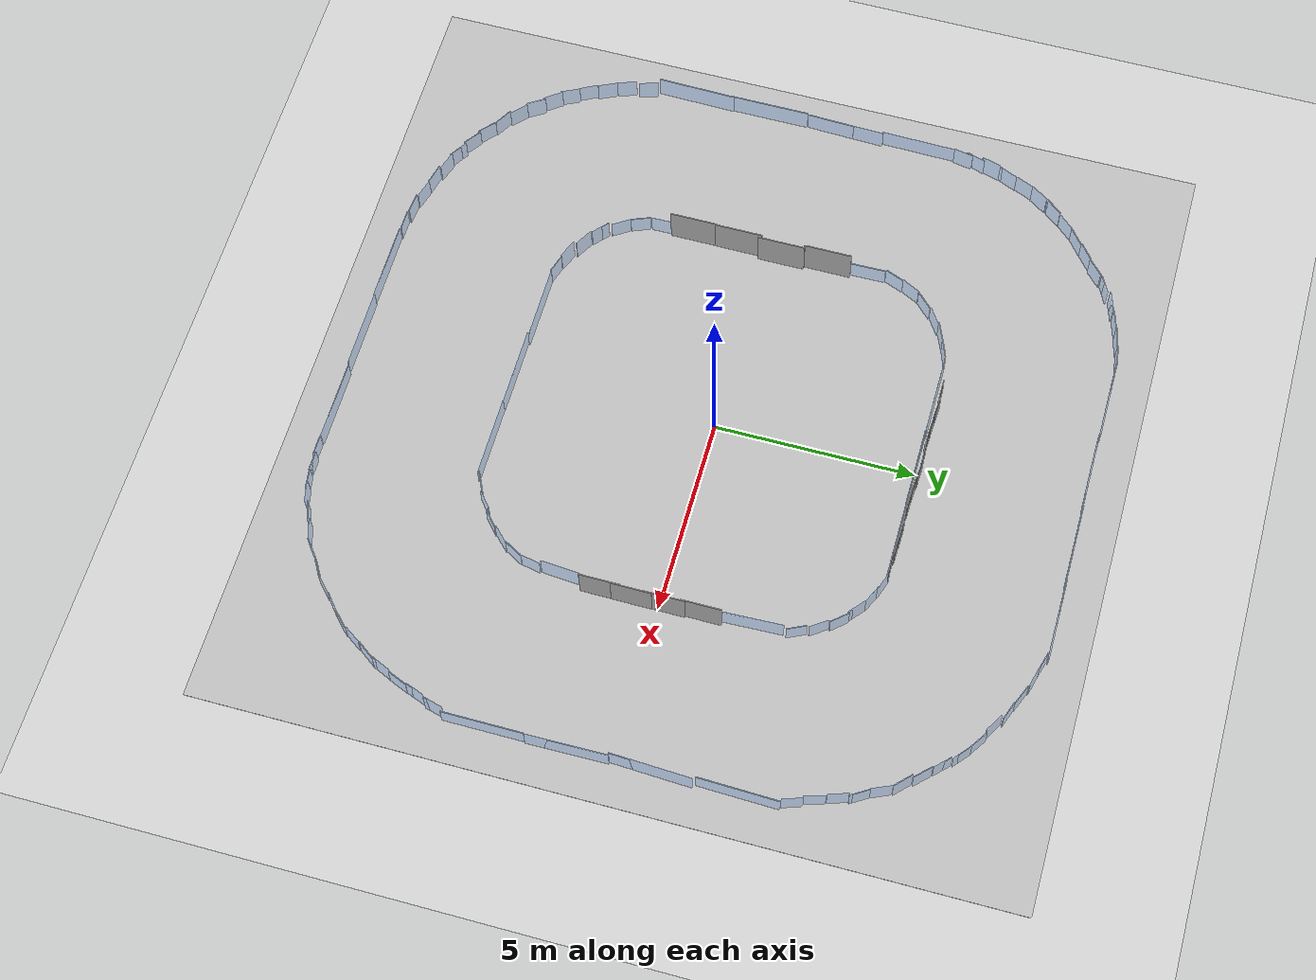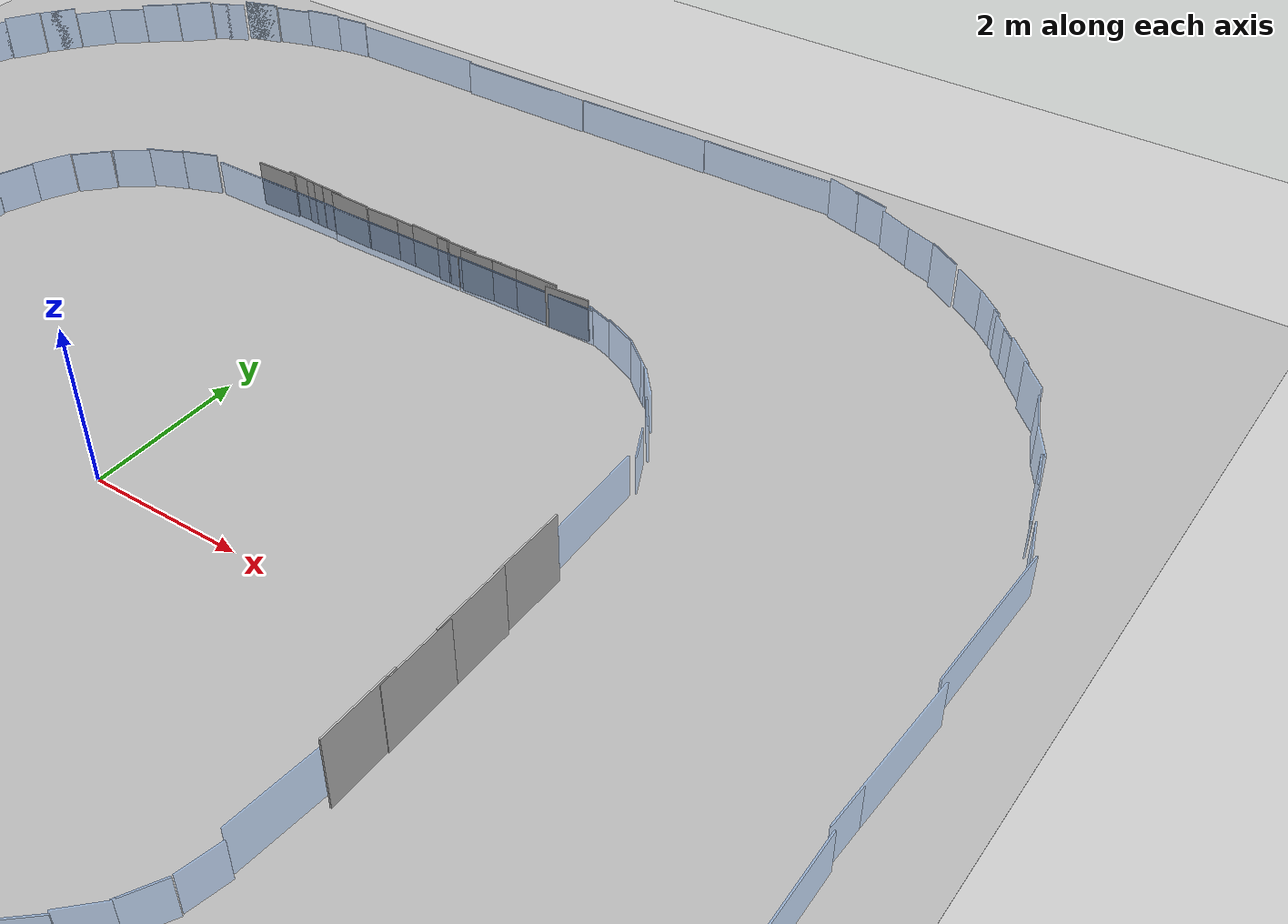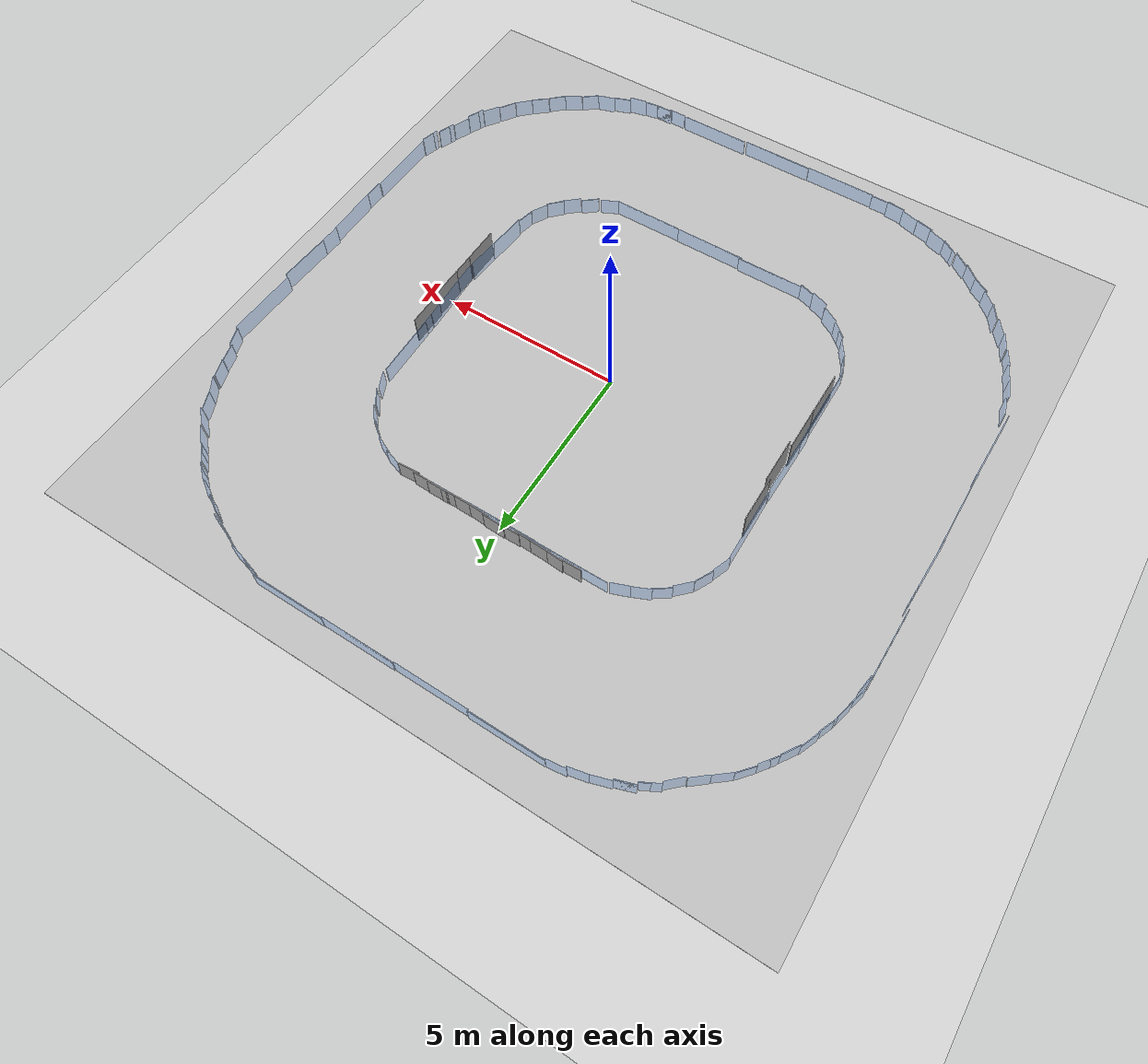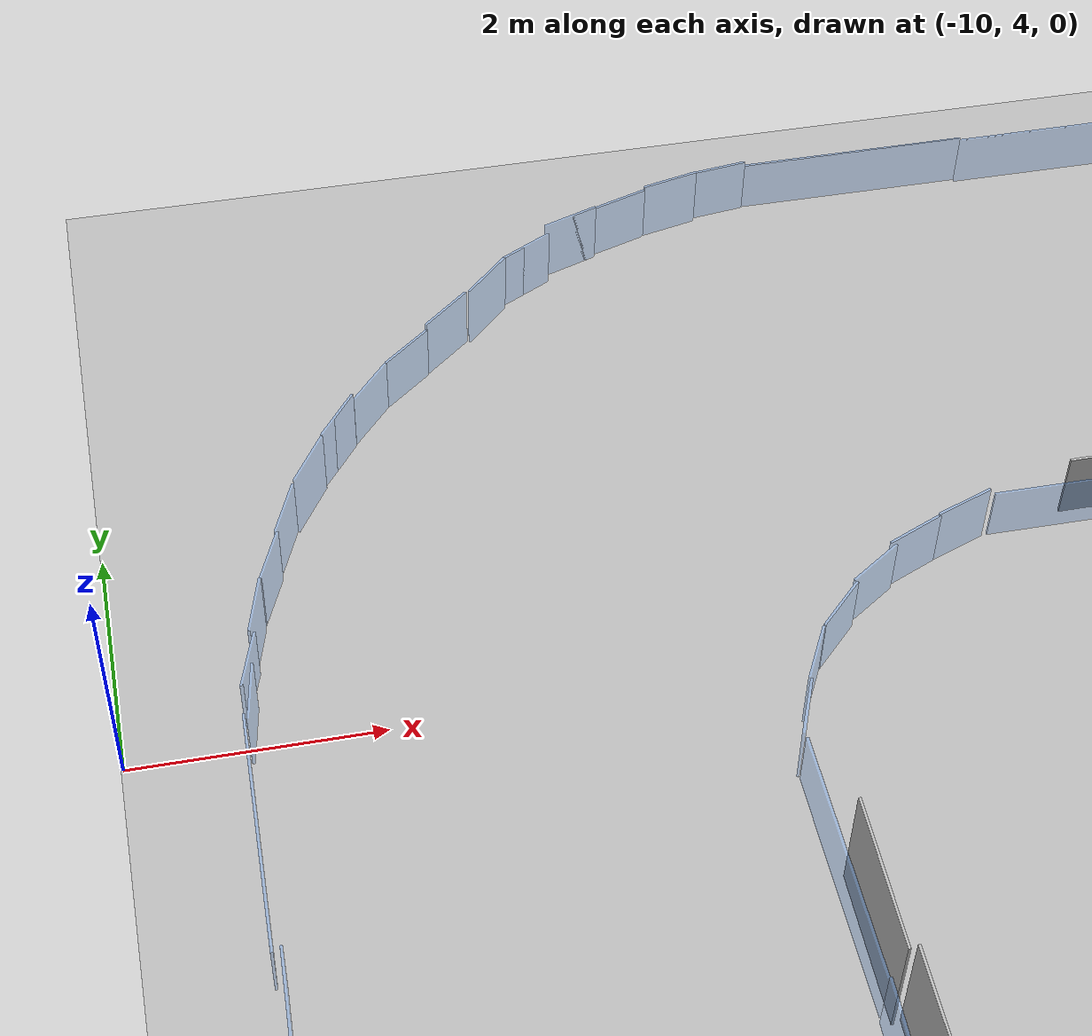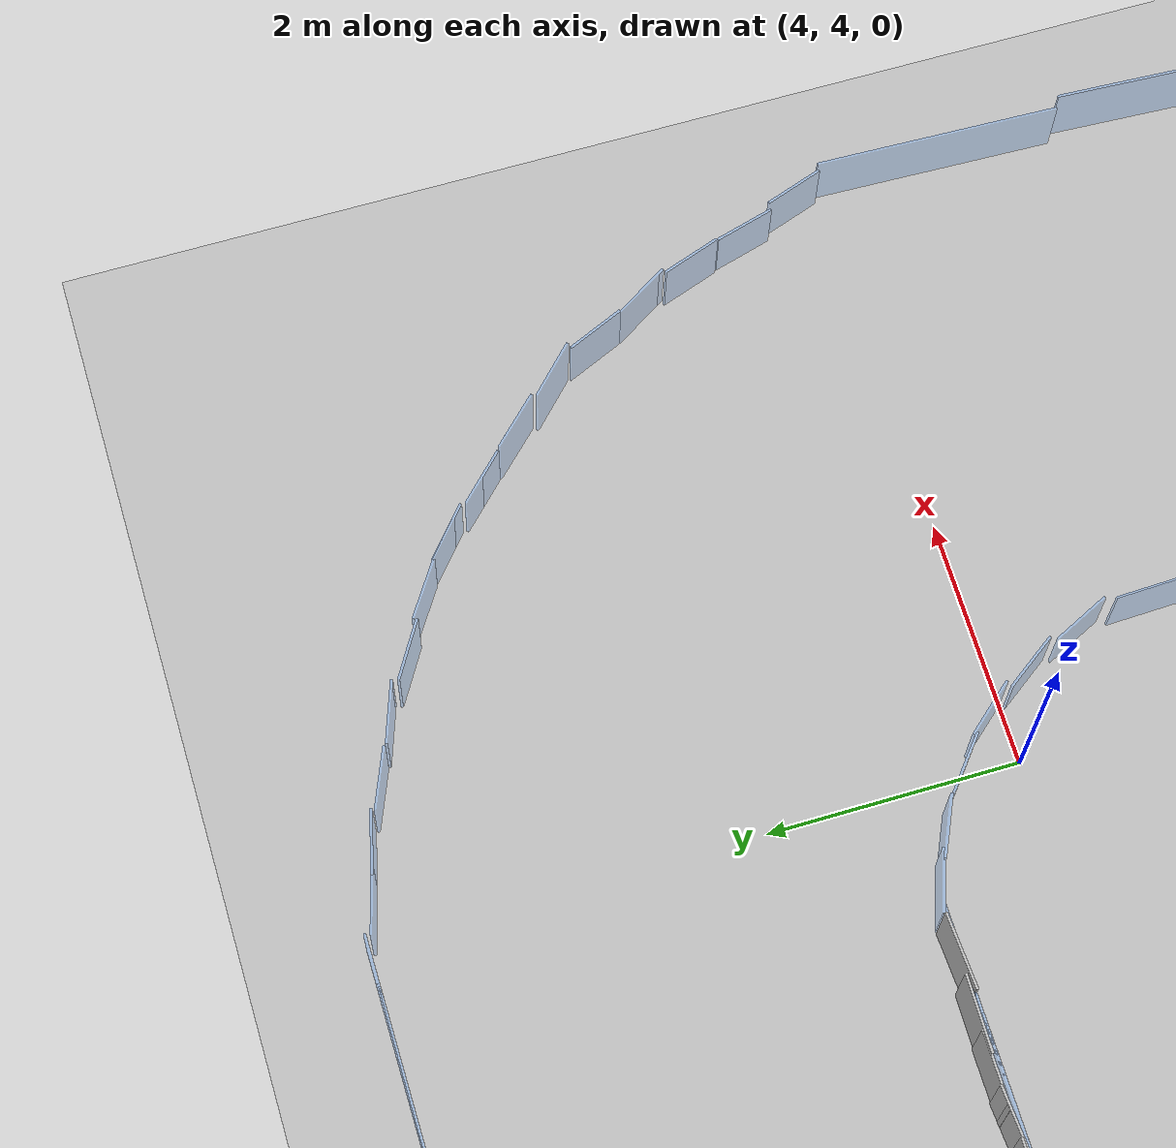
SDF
<sdf version="1.7">
 <world name="saft_city_arena">
  <physics type="ode">
   <real_time_update_rate>500</real_time_update_rate>
   <max_step_size>0.002</max_step_size>
   <real_time_factor>1</real_time_factor>
  </physics>
  <light name="sun" type="directional">
   <pose>0 0 10 0 -0 0</pose>
   <diffuse>0.8 0.8 0.8 1</diffuse>
   <specular>0.2 0.2 0.2 1</specular>
   <attenuation>
    <range>1000</range>
    <constant>0.9</constant>
    <linear>0.01</linear>
    <quadratic>0.001</quadratic>
   </attenuation>
   <direction>-0.5 0.1 -0.9</direction>
   <spot><inner_angle>0</inner_angle><outer_angle>0</outer_angle><falloff>0</falloff></spot>
  </light>
  <model name="ground_plane">
   <static>1</static>
   <link name="link">
    <collision name="collision">
     <geometry><plane><normal>0 0 1</normal><size>100 100</size></plane></geometry>
     <surface>
      <contact><collide_bitmask>65535</collide_bitmask></contact>
      <friction><ode><mu>100</mu><mu2>50</mu2></ode></friction>
     </surface>
    </collision>
    <visual name="visual">
     <cast_shadows>0</cast_shadows>
     <geometry><plane><normal>0 0 1</normal><size>100 100</size></plane></geometry>
     <material>
      <script><uri>file://media/materials/scripts/gazebo.material</uri><name>Gazebo/Grey</name></script>
     </material>
    </visual>
   </link>
  </model>
  <model name="race_track">
   <pose>-0.01892 0.017455 0 0 -0 0</pose>
   <static>1</static>
   <link name="ground">
    <collision name="collision">
     <pose>0 0 -0.025 0 -0 0</pose>
     <geometry><box><size>20 20 0.08</size></box></geometry>
    </collision>
    <visual name="visual">
     <pose>0 0 0.005 0 -0 0</pose>
     <geometry><box><size>20 20 0.01</size></box></geometry>
     <material><script><uri>model://race_track</uri><name>race_track/ground</name></script></material>
    </visual>
   </link>
  </model>
  <gravity>0 0 -9.8</gravity>
  <magnetic_field>6e-06 2.3e-05 -4.2e-05</magnetic_field>
  <atmosphere type="adiabatic"/>
  <scene><ambient>0.4 0.4 0.4 1</ambient><background>0.7 0.7 0.7 1</background><shadows>1</shadows></scene>
  <spherical_coordinates>
   <surface_model>EARTH_WGS84</surface_model>
   <latitude_deg>0</latitude_deg>
   <longitude_deg>0</longitude_deg>
   <elevation>0</elevation>
   <heading_deg>0</heading_deg>
  </spherical_coordinates>
  <model name="trash_sign_01">
   <static>1</static>
   <link name="sign">
    <visual name="visual">
     <pose>0 0 0.1 0 -0 0</pose>
     <geometry><box><size>0.02 1 1</size></box></geometry>
     <material>
      <script>
       <uri>model://photo_signs/trash_sign_01/materials/scripts</uri>
       <uri>model://photo_signs/trash_sign_01/materials/textures</uri>
       <name>PhotoSign/trash_sign_01</name>
      </script>
     </material>
    </visual>
   </link>
   <pose>5.03179 -1.40382 0.327227 0 -0 0</pose>
  </model>
  <model name="trash_sign_02">
   <static>1</static>
   <link name="sign">
    <visual name="visual">
     <pose>0 0 0.1 0 -0 0</pose>
     <geometry><box><size>0.02 1 1</size></box></geometry>
     <material>
      <script>
       <uri>model://photo_signs/trash_sign_02/materials/scripts</uri>
       <uri>model://photo_signs/trash_sign_02/materials/textures</uri>
       <name>PhotoSign/trash_sign_02</name>
      </script>
     </material>
    </visual>
   </link>
   <pose>5.04017 -0.636448 0.309953 0 -0 0</pose>
  </model>
  <model name="trash_sign_03">
   <static>1</static>
   <link name="sign">
    <visual name="visual">
     <pose>0 0 0.1 0 -0 0</pose>
     <geometry><box><size>0.02 1 1</size></box></geometry>
     <material>
      <script>
       <uri>model://photo_signs/trash_sign_03/materials/scripts</uri>
       <uri>model://photo_signs/trash_sign_03/materials/textures</uri>
       <name>PhotoSign/trash_sign_03</name>
      </script>
     </material>
    </visual>
   </link>
   <pose>5.03698 0.168034 0.324503 0 -0 0</pose>
  </model>
  <model name="trash_sign_04">
   <static>1</static>
   <link name="sign">
    <visual name="visual">
     <pose>0 0 0.1 0 -0 0</pose>
     <geometry><box><size>0.02 1 1</size></box></geometry>
     <material>
      <script>
       <uri>model://photo_signs/trash_sign_04/materials/scripts</uri>
       <uri>model://photo_signs/trash_sign_04/materials/textures</uri>
       <name>PhotoSign/trash_sign_04</name>
      </script>
     </material>
    </visual>
   </link>
   <pose>5.01136 1.04539 0.304628 0 -0 0</pose>
  </model>
  <model name="building_sign_01">
   <static>1</static>
   <link name="sign">
    <visual name="visual">
     <pose>0 0 0.175 0 -0 0</pose>
     <geometry><box><size>0.02 1.2 1.2</size></box></geometry>
     <material>
      <script>
       <uri>model://photo_signs/building_sign_01/materials/scripts</uri>
       <uri>model://photo_signs/building_sign_01/materials/textures</uri>
       <name>PhotoSign/building_sign_01</name>
      </script>
     </material>
    </visual>
   </link>
   <pose>-4.98428 1.54626 0.247239 0 -0 0</pose>
  </model>
  <model name="building_sign_02">
   <static>1</static>
   <link name="sign">
    <visual name="visual">
     <pose>0 0 0.175 0 -0 0</pose>
     <geometry><box><size>0.02 1.2 1.2</size></box></geometry>
     <material>
      <script>
       <uri>model://photo_signs/building_sign_02/materials/scripts</uri>
       <uri>model://photo_signs/building_sign_02/materials/textures</uri>
       <name>PhotoSign/building_sign_02</name>
      </script>
     </material>
    </visual>
   </link>
   <pose>-4.91211 0.369082 0.244687 0 -0 0</pose>
  </model>
  <model name="building_sign_03">
   <static>1</static>
   <link name="sign">
    <visual name="visual">
     <pose>0 0 0.175 0 -0 0</pose>
     <geometry><box><size>0.02 1.2 1.2</size></box></geometry>
     <material>
      <script>
       <uri>model://photo_signs/building_sign_03/materials/scripts</uri>
       <uri>model://photo_signs/building_sign_03/materials/textures</uri>
       <name>PhotoSign/building_sign_03</name>
      </script>
     </material>
    </visual>
   </link>
   <pose>-4.99648 -0.747766 0.224309 0 -0 0</pose>
  </model>
  <model name="building_sign_04">
   <static>1</static>
   <link name="sign">
    <visual name="visual">
     <pose>0 0 0.175 0 -0 0</pose>
     <geometry><box><size>0.02 1.2 1.2</size></box></geometry>
     <material>
      <script>
       <uri>model://photo_signs/building_sign_04/materials/scripts</uri>
       <uri>model://photo_signs/building_sign_04/materials/textures</uri>
       <name>PhotoSign/building_sign_04</name>
      </script>
     </material>
    </visual>
   </link>
   <pose>-5.00213 -1.91043 0.243349 0 -0 0</pose>
  </model>
  <model name="person_sign_01">
   <static>1</static>
   <link name="sign">
    <visual name="visual">
     <pose>0 0 0.16 0 -0 0</pose>
     <geometry><box><size>0.02 0.6 0.62</size></box></geometry>
     <material>
      <script>
       <uri>model://photo_signs/person_sign_01/materials/scripts</uri>
       <uri>model://photo_signs/person_sign_01/materials/textures</uri>
       <name>PhotoSign/person_sign_01</name>
      </script>
     </material>
    </visual>
   </link>
   <pose>2.14956 5.05182 0.150774 0 0 -1.58447</pose>
  </model>
  <model name="person_sign_02">
   <static>1</static>
   <link name="sign">
    <visual name="visual">
     <pose>0 0 0.16 0 -0 0</pose>
     <geometry><box><size>0.02 0.6 0.62</size></box></geometry>
     <material>
      <script>
       <uri>model://photo_signs/person_sign_02/materials/scripts</uri>
       <uri>model://photo_signs/person_sign_02/materials/textures</uri>
       <name>PhotoSign/person_sign_02</name>
      </script>
     </material>
    </visual>
   </link>
   <pose>1.73394 5.06385 0.137015 0 0 -1.56904</pose>
  </model>
  <model name="person_sign_03">
   <static>1</static>
   <link name="sign">
    <visual name="visual">
     <pose>0 0 0.16 0 -0 0</pose>
     <geometry><box><size>0.02 0.6 0.62</size></box></geometry>
     <material>
      <script>
       <uri>model://photo_signs/person_sign_03/materials/scripts</uri>
       <uri>model://photo_signs/person_sign_03/materials/textures</uri>
       <name>PhotoSign/person_sign_03</name>
      </script>
     </material>
    </visual>
   </link>
   <pose>1.32292 5.05339 0.139864 0 0 -1.50844</pose>
  </model>
  <model name="person_sign_04">
   <static>1</static>
   <link name="sign">
    <visual name="visual">
     <pose>0 0 0.16 0 -0 0</pose>
     <geometry><box><size>0.02 0.6 0.62</size></box></geometry>
     <material>
      <script>
       <uri>model://photo_signs/person_sign_04/materials/scripts</uri>
       <uri>model://photo_signs/person_sign_04/materials/textures</uri>
       <name>PhotoSign/person_sign_04</name>
      </script>
     </material>
    </visual>
   </link>
   <pose>0.931752 5.06364 0.158173 0 0 -1.58189</pose>
  </model>
  <model name="person_sign_05">
   <static>1</static>
   <link name="sign">
    <visual name="visual">
     <pose>0 0 0.16 0 -0 0</pose>
     <geometry><box><size>0.02 0.6 0.62</size></box></geometry>
     <material>
      <script>
       <uri>model://photo_signs/person_sign_05/materials/scripts</uri>
       <uri>model://photo_signs/person_sign_05/materials/textures</uri>
       <name>PhotoSign/person_sign_05</name>
      </script>
     </material>
    </visual>
   </link>
   <pose>0.515768 5.07932 0.173126 0 0 -1.62224</pose>
  </model>
  <model name="person_sign_06">
   <static>1</static>
   <link name="sign">
    <visual name="visual">
     <pose>0 0 0.16 0 -0 0</pose>
     <geometry><box><size>0.02 0.6 0.62</size></box></geometry>
     <material>
      <script>
       <uri>model://photo_signs/person_sign_06/materials/scripts</uri>
       <uri>model://photo_signs/person_sign_06/materials/textures</uri>
       <name>PhotoSign/person_sign_06</name>
      </script>
     </material>
    </visual>
   </link>
   <pose>0.071031 5.11301 0.138445 0 0 -1.6041</pose>
  </model>
  <model name="person_sign_07">
   <static>1</static>
   <link name="sign">
    <visual name="visual">
     <pose>0 0 0.16 0 -0 0</pose>
     <geometry><box><size>0.02 0.6 0.62</size></box></geometry>
     <material>
      <script>
       <uri>model://photo_signs/person_sign_07/materials/scripts</uri>
       <uri>model://photo_signs/person_sign_07/materials/textures</uri>
       <name>PhotoSign/person_sign_07</name>
      </script>
     </material>
    </visual>
   </link>
   <pose>-0.349251 5.10924 0.145721 0 0 -1.55728</pose>
  </model>
  <model name="person_sign_08">
   <static>1</static>
   <link name="sign">
    <visual name="visual">
     <pose>0 0 0.16 0 -0 0</pose>
     <geometry><box><size>0.02 0.6 0.62</size></box></geometry>
     <material>
      <script>
       <uri>model://photo_signs/person_sign_08/materials/scripts</uri>
       <uri>model://photo_signs/person_sign_08/materials/textures</uri>
       <name>PhotoSign/person_sign_08</name>
      </script>
     </material>
    </visual>
   </link>
   <pose>-0.820761 5.0966 0.177459 0 0 -1.60914</pose>
  </model>
  <model name="person_sign_09">
   <static>1</static>
   <link name="sign">
    <visual name="visual">
     <pose>0 0 0.16 0 -0 0</pose>
     <geometry><box><size>0.02 0.6 0.62</size></box></geometry>
     <material>
      <script>
       <uri>model://photo_signs/person_sign_09/materials/scripts</uri>
       <uri>model://photo_signs/person_sign_09/materials/textures</uri>
       <name>PhotoSign/person_sign_09</name>
      </script>
     </material>
    </visual>
   </link>
   <pose>-1.26214 5.11592 0.19236 0 0 -1.6064</pose>
  </model>
  <model name="person_sign_10">
   <static>1</static>
   <link name="sign">
    <visual name="visual">
     <pose>0 0 0.16 0 -0 0</pose>
     <geometry><box><size>0.02 0.6 0.62</size></box></geometry>
     <material>
      <script>
       <uri>model://photo_signs/person_sign_10/materials/scripts</uri>
       <uri>model://photo_signs/person_sign_10/materials/textures</uri>
       <name>PhotoSign/person_sign_10</name>
      </script>
     </material>
    </visual>
   </link>
   <pose>-1.58387 5.13215 0.194342 0 0 -1.63895</pose>
  </model>
  <model name="person_sign_11">
   <static>1</static>
   <link name="sign">
    <visual name="visual">
     <pose>0 0 0.16 0 -0 0</pose>
     <geometry><box><size>0.02 0.6 0.62</size></box></geometry>
     <material>
      <script>
       <uri>model://photo_signs/person_sign_11/materials/scripts</uri>
       <uri>model://photo_signs/person_sign_11/materials/textures</uri>
       <name>PhotoSign/person_sign_11</name>
      </script>
     </material>
    </visual>
   </link>
   <pose>-2.07522 5.12272 0.182686 0 0 -1.56299</pose>
  </model>
  <model name="person_sign_12">
   <static>1</static>
   <link name="sign">
    <visual name="visual">
     <pose>0 0 0.16 0 -0 0</pose>
     <geometry><box><size>0.02 0.6 0.62</size></box></geometry>
     <material>
      <script>
       <uri>model://photo_signs/person_sign_12/materials/scripts</uri>
       <uri>model://photo_signs/person_sign_12/materials/textures</uri>
       <name>PhotoSign/person_sign_12</name>
      </script>
     </material>
    </visual>
   </link>
   <pose>2.62259 5.01801 0.129118 0 0 -1.52126</pose>
  </model>
  <model name="transparent_wall">
   <static>1</static>
   <link name="wall">
    <collision name="collision"><geometry><box><size>2 0.02 1</size></box></geometry></collision>
    <visual name="visual">
     <geometry><box><size>2 0.02 1</size></box></geometry>
     <material>
      <ambient>0.3 0.6 1 0.3</ambient>
      <diffuse>0.3 0.6 1 0.3</diffuse>
      <specular>0 0 0 0</specular>
      <emissive>0 0 0 0</emissive>
     </material>
    </visual>
   </link>
   <pose>-0.063638 -5.05574 0 0 -0 0</pose>
  </model>
  <model name="transparent_wall_0">
   <static>1</static>
   <link name="wall">
    <collision name="collision"><geometry><box><size>2 0.02 1</size></box></geometry></collision>
    <visual name="visual">
     <geometry><box><size>2 0.02 1</size></box></geometry>
     <material>
      <ambient>0.3 0.6 1 0.3</ambient>
      <diffuse>0.3 0.6 1 0.3</diffuse>
      <specular>0 0 0 0</specular>
      <emissive>0 0 0 0</emissive>
     </material>
    </visual>
   </link>
   <pose>-1.98522 -5.01412 0 0 -0 0</pose>
  </model>
  <model name="transparent_wall_1">
   <static>1</static>
   <link name="wall">
    <collision name="collision"><geometry><box><size>2 0.02 1</size></box></geometry></collision>
    <visual name="visual">
     <geometry><box><size>2 0.02 1</size></box></geometry>
     <material>
      <ambient>0.3 0.6 1 0.3</ambient>
      <diffuse>0.3 0.6 1 0.3</diffuse>
      <specular>0 0 0 0</specular>
      <emissive>0 0 0 0</emissive>
     </material>
    </visual>
   </link>
   <pose>-2.09189 -9.06095 0 0 -0 0</pose>
  </model>
  <model name="transparent_wall_2">
   <static>1</static>
   <link name="wall">
    <collision name="collision"><geometry><box><size>2 0.02 1</size></box></geometry></collision>
    <visual name="visual">
     <geometry><box><size>2 0.02 1</size></box></geometry>
     <material>
      <ambient>0.3 0.6 1 0.3</ambient>
      <diffuse>0.3 0.6 1 0.3</diffuse>
      <specular>0 0 0 0</specular>
      <emissive>0 0 0 0</emissive>
     </material>
    </visual>
   </link>
   <pose>-0.079167 -9.04363 0 0 -0 0</pose>
  </model>
  <model name="transparent_wall_3">
   <static>1</static>
   <link name="wall">
    <collision name="collision"><geometry><box><size>2 0.02 1</size></box></geometry></collision>
    <visual name="visual">
     <geometry><box><size>2 0.02 1</size></box></geometry>
     <material>
      <ambient>0.3 0.6 1 0.3</ambient>
      <diffuse>0.3 0.6 1 0.3</diffuse>
      <specular>0 0 0 0</specular>
      <emissive>0 0 0 0</emissive>
     </material>
    </visual>
   </link>
   <pose>1.97662 -9.01296 0 0 -0 0</pose>
  </model>
  <model name="transparent_wall_4">
   <static>1</static>
   <link name="wall">
    <collision name="collision"><geometry><box><size>2 0.02 1</size></box></geometry></collision>
    <visual name="visual">
     <geometry><box><size>2 0.02 1</size></box></geometry>
     <material>
      <ambient>0.3 0.6 1 0.3</ambient>
      <diffuse>0.3 0.6 1 0.3</diffuse>
      <specular>0 0 0 0</specular>
      <emissive>0 0 0 0</emissive>
     </material>
    </visual>
   </link>
   <pose>1.93743 -5.06455 0 0 -0 0</pose>
  </model>
  <model name="transparent_wall_5">
   <static>1</static>
   <link name="wall">
    <collision name="collision"><geometry><box><size>2 0.02 1</size></box></geometry></collision>
    <visual name="visual">
     <geometry><box><size>2 0.02 1</size></box></geometry>
     <material>
      <ambient>0.3 0.6 1 0.3</ambient>
      <diffuse>0.3 0.6 1 0.3</diffuse>
      <specular>0 0 0 0</specular>
      <emissive>0 0 0 0</emissive>
     </material>
    </visual>
   </link>
   <pose>-5.05108 -2.0249 0.028425 0 0 -1.56328</pose>
  </model>
  <model name="transparent_wall_6">
   <static>1</static>
   <link name="wall">
    <collision name="collision"><geometry><box><size>2 0.02 1</size></box></geometry></collision>
    <visual name="visual">
     <geometry><box><size>2 0.02 1</size></box></geometry>
     <material>
      <ambient>0.3 0.6 1 0.3</ambient>
      <diffuse>0.3 0.6 1 0.3</diffuse>
      <specular>0 0 0 0</specular>
      <emissive>0 0 0 0</emissive>
     </material>
    </visual>
   </link>
   <pose>-5.07219 -0.024101 0.128366 0 -0 1.55488</pose>
  </model>
  <model name="transparent_wall_7">
   <static>1</static>
   <link name="wall">
    <collision name="collision"><geometry><box><size>2 0.02 1</size></box></geometry></collision>
    <visual name="visual">
     <geometry><box><size>2 0.02 1</size></box></geometry>
     <material>
      <ambient>0.3 0.6 1 0.3</ambient>
      <diffuse>0.3 0.6 1 0.3</diffuse>
      <specular>0 0 0 0</specular>
      <emissive>0 0 0 0</emissive>
     </material>
    </visual>
   </link>
   <pose>-5.06249 2.00981 0.041984 0 -0 1.58519</pose>
  </model>
  <model name="transparent_wall_8">
   <static>1</static>
   <link name="wall">
    <collision name="collision"><geometry><box><size>2 0.02 1</size></box></geometry></collision>
    <visual name="visual">
     <geometry><box><size>2 0.02 1</size></box></geometry>
     <material>
      <ambient>0.3 0.6 1 0.3</ambient>
      <diffuse>0.3 0.6 1 0.3</diffuse>
      <specular>0 0 0 0</specular>
      <emissive>0 0 0 0</emissive>
     </material>
    </visual>
   </link>
   <pose>4.8982 -1.90916 0.141159 0 0 -1.65353</pose>
  </model>
  <model name="transparent_wall_9">
   <static>1</static>
   <link name="wall">
    <collision name="collision"><geometry><box><size>2 0.02 1</size></box></geometry></collision>
    <visual name="visual">
     <geometry><box><size>2 0.02 1</size></box></geometry>
     <material>
      <ambient>0.3 0.6 1 0.3</ambient>
      <diffuse>0.3 0.6 1 0.3</diffuse>
      <specular>0 0 0 0</specular>
      <emissive>0 0 0 0</emissive>
     </material>
    </visual>
   </link>
   <pose>4.98103 0.003821 0.088769 0 0 -1.51702</pose>
  </model>
  <model name="transparent_wall_10">
   <static>1</static>
   <link name="wall">
    <collision name="collision"><geometry><box><size>2 0.02 1</size></box></geometry></collision>
    <visual name="visual">
     <geometry><box><size>2 0.02 1</size></box></geometry>
     <material>
      <ambient>0.3 0.6 1 0.3</ambient>
      <diffuse>0.3 0.6 1 0.3</diffuse>
      <specular>0 0 0 0</specular>
      <emissive>0 0 0 0</emissive>
     </material>
    </visual>
   </link>
   <pose>4.90263 2.00371 0.067201 0 -0 1.60296</pose>
  </model>
  <model name="transparent_wall_11">
   <static>1</static>
   <link name="wall">
    <collision name="collision"><geometry><box><size>2 0.02 1</size></box></geometry></collision>
    <visual name="visual">
     <geometry><box><size>2 0.02 1</size></box></geometry>
     <material>
      <ambient>0.3 0.6 1 0.3</ambient>
      <diffuse>0.3 0.6 1 0.3</diffuse>
      <specular>0 0 0 0</specular>
      <emissive>0 0 0 0</emissive>
     </material>
    </visual>
   </link>
   <pose>2.00706 5.00496 0 0 -0 0</pose>
  </model>
  <model name="transparent_wall_12">
   <static>1</static>
   <link name="wall">
    <collision name="collision"><geometry><box><size>2 0.02 1</size></box></geometry></collision>
    <visual name="visual">
     <geometry><box><size>2 0.02 1</size></box></geometry>
     <material>
      <ambient>0.3 0.6 1 0.3</ambient>
      <diffuse>0.3 0.6 1 0.3</diffuse>
      <specular>0 0 0 0</specular>
      <emissive>0 0 0 0</emissive>
     </material>
    </visual>
   </link>
   <pose>-0.012906 4.99693 0 0 -0 0</pose>
  </model>
  <model name="transparent_wall_13">
   <static>1</static>
   <link name="wall">
    <collision name="collision"><geometry><box><size>2 0.02 1</size></box></geometry></collision>
    <visual name="visual">
     <geometry><box><size>2 0.02 1</size></box></geometry>
     <material>
      <ambient>0.3 0.6 1 0.3</ambient>
      <diffuse>0.3 0.6 1 0.3</diffuse>
      <specular>0 0 0 0</specular>
      <emissive>0 0 0 0</emissive>
     </material>
    </visual>
   </link>
   <pose>-2.00866 5.01257 0 0 -0 0</pose>
  </model>
  <model name="transparent_wall_short">
   <static>1</static>
   <link name="wall">
    <collision name="collision"><geometry><box><size>0.5 0.02 1</size></box></geometry></collision>
    <visual name="visual">
     <geometry><box><size>0.5 0.02 1</size></box></geometry>
     <material>
      <ambient>0.3 0.6 1 0.3</ambient>
      <diffuse>0.3 0.6 1 0.3</diffuse>
      <specular>0 0 0 0</specular>
      <emissive>0 0 0 0</emissive>
     </material>
    </visual>
   </link>
   <pose>-4.94708 -3.28797 0.040987 0 0 -1.18648</pose>
  </model>
  <model name="transparent_wall_short_0">
   <static>1</static>
   <link name="wall">
    <collision name="collision"><geometry><box><size>0.5 0.02 1</size></box></geometry></collision>
    <visual name="visual">
     <geometry><box><size>0.5 0.02 1</size></box></geometry>
     <material>
      <ambient>0.3 0.6 1 0.3</ambient>
      <diffuse>0.3 0.6 1 0.3</diffuse>
      <specular>0 0 0 0</specular>
      <emissive>0 0 0 0</emissive>
     </material>
    </visual>
   </link>
   <pose>-4.7203 -3.73547 0.029213 0 0 -0.987347</pose>
  </model>
  <model name="transparent_wall_short_1">
   <static>1</static>
   <link name="wall">
    <collision name="collision"><geometry><box><size>0.5 0.02 1</size></box></geometry></collision>
    <visual name="visual">
     <geometry><box><size>0.5 0.02 1</size></box></geometry>
     <material>
      <ambient>0.3 0.6 1 0.3</ambient>
      <diffuse>0.3 0.6 1 0.3</diffuse>
      <specular>0 0 0 0</specular>
      <emissive>0 0 0 0</emissive>
     </material>
    </visual>
   </link>
   <pose>-4.37851 -4.17919 0.107006 0 0 -0.722057</pose>
  </model>
  <model name="transparent_wall_short_2">
   <static>1</static>
   <link name="wall">
    <collision name="collision"><geometry><box><size>0.5 0.02 1</size></box></geometry></collision>
    <visual name="visual">
     <geometry><box><size>0.5 0.02 1</size></box></geometry>
     <material>
      <ambient>0.3 0.6 1 0.3</ambient>
      <diffuse>0.3 0.6 1 0.3</diffuse>
      <specular>0 0 0 0</specular>
      <emissive>0 0 0 0</emissive>
     </material>
    </visual>
   </link>
   <pose>-3.96842 -4.49368 0.136805 0 0 -0.518828</pose>
  </model>
  <model name="transparent_wall_short_3">
   <static>1</static>
   <link name="wall">
    <collision name="collision"><geometry><box><size>0.5 0.02 1</size></box></geometry></collision>
    <visual name="visual">
     <geometry><box><size>0.5 0.02 1</size></box></geometry>
     <material>
      <ambient>0.3 0.6 1 0.3</ambient>
      <diffuse>0.3 0.6 1 0.3</diffuse>
      <specular>0 0 0 0</specular>
      <emissive>0 0 0 0</emissive>
     </material>
    </visual>
   </link>
   <pose>-3.51803 -4.77775 0.183505 0 0 -0.369282</pose>
  </model>
  <model name="transparent_wall_short_4">
   <static>1</static>
   <link name="wall">
    <collision name="collision"><geometry><box><size>0.5 0.02 1</size></box></geometry></collision>
    <visual name="visual">
     <geometry><box><size>0.5 0.02 1</size></box></geometry>
     <material>
      <ambient>0.3 0.6 1 0.3</ambient>
      <diffuse>0.3 0.6 1 0.3</diffuse>
      <specular>0 0 0 0</specular>
      <emissive>0 0 0 0</emissive>
     </material>
    </visual>
   </link>
   <pose>-3.10991 -4.93677 0.093668 0 0 -0.308535</pose>
  </model>
  <model name="transparent_wall_short_5">
   <static>1</static>
   <link name="wall">
    <collision name="collision"><geometry><box><size>0.5 0.02 1</size></box></geometry></collision>
    <visual name="visual">
     <geometry><box><size>0.5 0.02 1</size></box></geometry>
     <material>
      <ambient>0.3 0.6 1 0.3</ambient>
      <diffuse>0.3 0.6 1 0.3</diffuse>
      <specular>0 0 0 0</specular>
      <emissive>0 0 0 0</emissive>
     </material>
    </visual>
   </link>
   <pose>3.11225 -4.94553 0.008288 0 -0 0.440215</pose>
  </model>
  <model name="transparent_wall_short_6">
   <static>1</static>
   <link name="wall">
    <collision name="collision"><geometry><box><size>0.5 0.02 1</size></box></geometry></collision>
    <visual name="visual">
     <geometry><box><size>0.5 0.02 1</size></box></geometry>
     <material>
      <ambient>0.3 0.6 1 0.3</ambient>
      <diffuse>0.3 0.6 1 0.3</diffuse>
      <specular>0 0 0 0</specular>
      <emissive>0 0 0 0</emissive>
     </material>
    </visual>
   </link>
   <pose>3.58736 -4.68834 0.024846 0 -0 0.688681</pose>
  </model>
  <model name="transparent_wall_short_7">
   <static>1</static>
   <link name="wall">
    <collision name="collision"><geometry><box><size>0.5 0.02 1</size></box></geometry></collision>
    <visual name="visual">
     <geometry><box><size>0.5 0.02 1</size></box></geometry>
     <material>
      <ambient>0.3 0.6 1 0.3</ambient>
      <diffuse>0.3 0.6 1 0.3</diffuse>
      <specular>0 0 0 0</specular>
      <emissive>0 0 0 0</emissive>
     </material>
    </visual>
   </link>
   <pose>4.02029 -4.40085 0.035984 0 -0 0.715586</pose>
  </model>
  <model name="transparent_wall_short_8">
   <static>1</static>
   <link name="wall">
    <collision name="collision"><geometry><box><size>0.5 0.02 1</size></box></geometry></collision>
    <visual name="visual">
     <geometry><box><size>0.5 0.02 1</size></box></geometry>
     <material>
      <ambient>0.3 0.6 1 0.3</ambient>
      <diffuse>0.3 0.6 1 0.3</diffuse>
      <specular>0 0 0 0</specular>
      <emissive>0 0 0 0</emissive>
     </material>
    </visual>
   </link>
   <pose>4.36224 -4.04912 0.049637 0 -0 0.783063</pose>
  </model>
  <model name="transparent_wall_short_9">
   <static>1</static>
   <link name="wall">
    <collision name="collision"><geometry><box><size>0.5 0.02 1</size></box></geometry></collision>
    <visual name="visual">
     <geometry><box><size>0.5 0.02 1</size></box></geometry>
     <material>
      <ambient>0.3 0.6 1 0.3</ambient>
      <diffuse>0.3 0.6 1 0.3</diffuse>
      <specular>0 0 0 0</specular>
      <emissive>0 0 0 0</emissive>
     </material>
    </visual>
   </link>
   <pose>4.63881 -3.651 0.033295 -0.016287 -0.009075 1.06248</pose>
  </model>
  <model name="transparent_wall_short_10">
   <static>1</static>
   <link name="wall">
    <collision name="collision"><geometry><box><size>0.5 0.02 1</size></box></geometry></collision>
    <visual name="visual">
     <geometry><box><size>0.5 0.02 1</size></box></geometry>
     <material>
      <ambient>0.3 0.6 1 0.3</ambient>
      <diffuse>0.3 0.6 1 0.3</diffuse>
      <specular>0 0 0 0</specular>
      <emissive>0 0 0 0</emissive>
     </material>
    </visual>
   </link>
   <pose>4.80251 -3.16733 0.029548 0 -0 1.36219</pose>
  </model>
  <model name="transparent_wall_short_11">
   <static>1</static>
   <link name="wall">
    <collision name="collision"><geometry><box><size>0.5 0.02 1</size></box></geometry></collision>
    <visual name="visual">
     <geometry><box><size>0.5 0.02 1</size></box></geometry>
     <material>
      <ambient>0.3 0.6 1 0.3</ambient>
      <diffuse>0.3 0.6 1 0.3</diffuse>
      <specular>0 0 0 0</specular>
      <emissive>0 0 0 0</emissive>
     </material>
    </visual>
   </link>
   <pose>4.80907 3.2971 0.020246 0 0 -1.12421</pose>
  </model>
  <model name="transparent_wall_short_12">
   <static>1</static>
   <link name="wall">
    <collision name="collision"><geometry><box><size>0.5 0.02 1</size></box></geometry></collision>
    <visual name="visual">
     <geometry><box><size>0.5 0.02 1</size></box></geometry>
     <material>
      <ambient>0.3 0.6 1 0.3</ambient>
      <diffuse>0.3 0.6 1 0.3</diffuse>
      <specular>0 0 0 0</specular>
      <emissive>0 0 0 0</emissive>
     </material>
    </visual>
   </link>
   <pose>4.58747 3.77696 0.026694 0 0 -0.949792</pose>
  </model>
  <model name="transparent_wall_short_13">
   <static>1</static>
   <link name="wall">
    <collision name="collision"><geometry><box><size>0.5 0.02 1</size></box></geometry></collision>
    <visual name="visual">
     <geometry><box><size>0.5 0.02 1</size></box></geometry>
     <material>
      <ambient>0.3 0.6 1 0.3</ambient>
      <diffuse>0.3 0.6 1 0.3</diffuse>
      <specular>0 0 0 0</specular>
      <emissive>0 0 0 0</emissive>
     </material>
    </visual>
   </link>
   <pose>4.32065 4.19695 0.051881 0 0 -0.856989</pose>
  </model>
  <model name="transparent_wall_short_14">
   <static>1</static>
   <link name="wall">
    <collision name="collision"><geometry><box><size>0.5 0.02 1</size></box></geometry></collision>
    <visual name="visual">
     <geometry><box><size>0.5 0.02 1</size></box></geometry>
     <material>
      <ambient>0.3 0.6 1 0.3</ambient>
      <diffuse>0.3 0.6 1 0.3</diffuse>
      <specular>0 0 0 0</specular>
      <emissive>0 0 0 0</emissive>
     </material>
    </visual>
   </link>
   <pose>3.96315 4.51815 0.08493 0 0 -0.687549</pose>
  </model>
  <model name="transparent_wall_short_15">
   <static>1</static>
   <link name="wall">
    <collision name="collision"><geometry><box><size>0.5 0.02 1</size></box></geometry></collision>
    <visual name="visual">
     <geometry><box><size>0.5 0.02 1</size></box></geometry>
     <material>
      <ambient>0.3 0.6 1 0.3</ambient>
      <diffuse>0.3 0.6 1 0.3</diffuse>
      <specular>0 0 0 0</specular>
      <emissive>0 0 0 0</emissive>
     </material>
    </visual>
   </link>
   <pose>3.54274 4.79572 0.065202 0 0 -0.429976</pose>
  </model>
  <model name="transparent_wall_short_16">
   <static>1</static>
   <link name="wall">
    <collision name="collision"><geometry><box><size>0.5 0.02 1</size></box></geometry></collision>
    <visual name="visual">
     <geometry><box><size>0.5 0.02 1</size></box></geometry>
     <material>
      <ambient>0.3 0.6 1 0.3</ambient>
      <diffuse>0.3 0.6 1 0.3</diffuse>
      <specular>0 0 0 0</specular>
      <emissive>0 0 0 0</emissive>
     </material>
    </visual>
   </link>
   <pose>3.17105 4.95409 0.02787 0 0 -0.324928</pose>
  </model>
  <model name="transparent_wall_short_17">
   <static>1</static>
   <link name="wall">
    <collision name="collision"><geometry><box><size>0.5 0.02 1</size></box></geometry></collision>
    <visual name="visual">
     <geometry><box><size>0.5 0.02 1</size></box></geometry>
     <material>
      <ambient>0.3 0.6 1 0.3</ambient>
      <diffuse>0.3 0.6 1 0.3</diffuse>
      <specular>0 0 0 0</specular>
      <emissive>0 0 0 0</emissive>
     </material>
    </visual>
   </link>
   <pose>-3.29522 4.91907 0.079268 0 -0 0.353213</pose>
  </model>
  <model name="transparent_wall_short_18">
   <static>1</static>
   <link name="wall">
    <collision name="collision"><geometry><box><size>0.5 0.02 1</size></box></geometry></collision>
    <visual name="visual">
     <geometry><box><size>0.5 0.02 1</size></box></geometry>
     <material>
      <ambient>0.3 0.6 1 0.3</ambient>
      <diffuse>0.3 0.6 1 0.3</diffuse>
      <specular>0 0 0 0</specular>
      <emissive>0 0 0 0</emissive>
     </material>
    </visual>
   </link>
   <pose>-3.74482 4.73577 0.064179 0 -0 0.407671</pose>
  </model>
  <model name="transparent_wall_short_19">
   <static>1</static>
   <link name="wall">
    <collision name="collision"><geometry><box><size>0.5 0.02 1</size></box></geometry></collision>
    <visual name="visual">
     <geometry><box><size>0.5 0.02 1</size></box></geometry>
     <material>
      <ambient>0.3 0.6 1 0.3</ambient>
      <diffuse>0.3 0.6 1 0.3</diffuse>
      <specular>0 0 0 0</specular>
      <emissive>0 0 0 0</emissive>
     </material>
    </visual>
   </link>
   <pose>-4.13752 4.4844 0.046875 0 -0 0.590745</pose>
  </model>
  <model name="transparent_wall_short_20">
   <static>1</static>
   <link name="wall">
    <collision name="collision"><geometry><box><size>0.5 0.02 1</size></box></geometry></collision>
    <visual name="visual">
     <geometry><box><size>0.5 0.02 1</size></box></geometry>
     <material>
      <ambient>0.3 0.6 1 0.3</ambient>
      <diffuse>0.3 0.6 1 0.3</diffuse>
      <specular>0 0 0 0</specular>
      <emissive>0 0 0 0</emissive>
     </material>
    </visual>
   </link>
   <pose>-4.50886 4.13866 0.064163 0 -0 0.783613</pose>
  </model>
  <model name="transparent_wall_short_21">
   <static>1</static>
   <link name="wall">
    <collision name="collision"><geometry><box><size>0.5 0.02 1</size></box></geometry></collision>
    <visual name="visual">
     <geometry><box><size>0.5 0.02 1</size></box></geometry>
     <material>
      <ambient>0.3 0.6 1 0.3</ambient>
      <diffuse>0.3 0.6 1 0.3</diffuse>
      <specular>0 0 0 0</specular>
      <emissive>0 0 0 0</emissive>
     </material>
    </visual>
   </link>
   <pose>-4.8132 3.72803 0.071165 0 -0 1.09326</pose>
  </model>
  <model name="transparent_wall_short_22">
   <static>1</static>
   <link name="wall">
    <collision name="collision"><geometry><box><size>0.5 0.02 1</size></box></geometry></collision>
    <visual name="visual">
     <geometry><box><size>0.5 0.02 1</size></box></geometry>
     <material>
      <ambient>0.3 0.6 1 0.3</ambient>
      <diffuse>0.3 0.6 1 0.3</diffuse>
      <specular>0 0 0 0</specular>
      <emissive>0 0 0 0</emissive>
     </material>
    </visual>
   </link>
   <pose>-5.00622 3.26337 0.071421 0 -0 1.20118</pose>
  </model>
  <model name="transparent_wall_14">
   <static>1</static>
   <link name="wall">
    <collision name="collision"><geometry><box><size>2 0.02 1</size></box></geometry></collision>
    <visual name="visual">
     <geometry><box><size>2 0.02 1</size></box></geometry>
     <material>
      <ambient>0.3 0.6 1 0.3</ambient>
      <diffuse>0.3 0.6 1 0.3</diffuse>
      <specular>0 0 0 0</specular>
      <emissive>0 0 0 0</emissive>
     </material>
    </visual>
   </link>
   <pose>-9.09276 -2.96726 0.139382 0 0 -1.59061</pose>
  </model>
  <model name="transparent_wall_15">
   <static>1</static>
   <link name="wall">
    <collision name="collision"><geometry><box><size>2 0.02 1</size></box></geometry></collision>
    <visual name="visual">
     <geometry><box><size>2 0.02 1</size></box></geometry>
     <material>
      <ambient>0.3 0.6 1 0.3</ambient>
      <diffuse>0.3 0.6 1 0.3</diffuse>
      <specular>0 0 0 0</specular>
      <emissive>0 0 0 0</emissive>
     </material>
    </visual>
   </link>
   <pose>-9.09233 -1.01612 0.12544 0 0 -1.57159</pose>
  </model>
  <model name="transparent_wall_16">
   <static>1</static>
   <link name="wall">
    <collision name="collision"><geometry><box><size>2 0.02 1</size></box></geometry></collision>
    <visual name="visual">
     <geometry><box><size>2 0.02 1</size></box></geometry>
     <material>
      <ambient>0.3 0.6 1 0.3</ambient>
      <diffuse>0.3 0.6 1 0.3</diffuse>
      <specular>0 0 0 0</specular>
      <emissive>0 0 0 0</emissive>
     </material>
    </visual>
   </link>
   <pose>-9.07089 0.997301 0.061654 0 0 -1.60555</pose>
  </model>
  <model name="transparent_wall_17">
   <static>1</static>
   <link name="wall">
    <collision name="collision"><geometry><box><size>2 0.02 1</size></box></geometry></collision>
    <visual name="visual">
     <geometry><box><size>2 0.02 1</size></box></geometry>
     <material>
      <ambient>0.3 0.6 1 0.3</ambient>
      <diffuse>0.3 0.6 1 0.3</diffuse>
      <specular>0 0 0 0</specular>
      <emissive>0 0 0 0</emissive>
     </material>
    </visual>
   </link>
   <pose>-9.08816 2.97502 0.023913 0 0 -1.58889</pose>
  </model>
  <model name="transparent_wall_18">
   <static>1</static>
   <link name="wall">
    <collision name="collision"><geometry><box><size>2 0.02 1</size></box></geometry></collision>
    <visual name="visual">
     <geometry><box><size>2 0.02 1</size></box></geometry>
     <material>
      <ambient>0.3 0.6 1 0.3</ambient>
      <diffuse>0.3 0.6 1 0.3</diffuse>
      <specular>0 0 0 0</specular>
      <emissive>0 0 0 0</emissive>
     </material>
    </visual>
   </link>
   <pose>-3.02083 9.08937 0 0 -0 0</pose>
  </model>
  <model name="transparent_wall_19">
   <static>1</static>
   <link name="wall">
    <collision name="collision"><geometry><box><size>2 0.02 1</size></box></geometry></collision>
    <visual name="visual">
     <geometry><box><size>2 0.02 1</size></box></geometry>
     <material>
      <ambient>0.3 0.6 1 0.3</ambient>
      <diffuse>0.3 0.6 1 0.3</diffuse>
      <specular>0 0 0 0</specular>
      <emissive>0 0 0 0</emissive>
     </material>
    </visual>
   </link>
   <pose>-1.02556 9.06492 0 0 -0 0</pose>
  </model>
  <model name="transparent_wall_20">
   <static>1</static>
   <link name="wall">
    <collision name="collision"><geometry><box><size>2 0.02 1</size></box></geometry></collision>
    <visual name="visual">
     <geometry><box><size>2 0.02 1</size></box></geometry>
     <material>
      <ambient>0.3 0.6 1 0.3</ambient>
      <diffuse>0.3 0.6 1 0.3</diffuse>
      <specular>0 0 0 0</specular>
      <emissive>0 0 0 0</emissive>
     </material>
    </visual>
   </link>
   <pose>0.982394 9.07937 0 0 -0 0</pose>
  </model>
  <model name="transparent_wall_21">
   <static>1</static>
   <link name="wall">
    <collision name="collision"><geometry><box><size>2 0.02 1</size></box></geometry></collision>
    <visual name="visual">
     <geometry><box><size>2 0.02 1</size></box></geometry>
     <material>
      <ambient>0.3 0.6 1 0.3</ambient>
      <diffuse>0.3 0.6 1 0.3</diffuse>
      <specular>0 0 0 0</specular>
      <emissive>0 0 0 0</emissive>
     </material>
    </visual>
   </link>
   <pose>2.97679 9.09387 0 0 -0 0</pose>
  </model>
  <model name="transparent_wall_22">
   <static>1</static>
   <link name="wall">
    <collision name="collision"><geometry><box><size>2 0.02 1</size></box></geometry></collision>
    <visual name="visual">
     <geometry><box><size>2 0.02 1</size></box></geometry>
     <material>
      <ambient>0.3 0.6 1 0.3</ambient>
      <diffuse>0.3 0.6 1 0.3</diffuse>
      <specular>0 0 0 0</specular>
      <emissive>0 0 0 0</emissive>
     </material>
    </visual>
   </link>
   <pose>8.99488 3.00669 0.061624 0 -0 1.54291</pose>
  </model>
  <model name="transparent_wall_23">
   <static>1</static>
   <link name="wall">
    <collision name="collision"><geometry><box><size>2 0.02 1</size></box></geometry></collision>
    <visual name="visual">
     <geometry><box><size>2 0.02 1</size></box></geometry>
     <material>
      <ambient>0.3 0.6 1 0.3</ambient>
      <diffuse>0.3 0.6 1 0.3</diffuse>
      <specular>0 0 0 0</specular>
      <emissive>0 0 0 0</emissive>
     </material>
    </visual>
   </link>
   <pose>8.99872 0.973942 0.103328 0 -0 1.52396</pose>
  </model>
  <model name="transparent_wall_24">
   <static>1</static>
   <link name="wall">
    <collision name="collision"><geometry><box><size>2 0.02 1</size></box></geometry></collision>
    <visual name="visual">
     <geometry><box><size>2 0.02 1</size></box></geometry>
     <material>
      <ambient>0.3 0.6 1 0.3</ambient>
      <diffuse>0.3 0.6 1 0.3</diffuse>
      <specular>0 0 0 0</specular>
      <emissive>0 0 0 0</emissive>
     </material>
    </visual>
   </link>
   <pose>9.00601 -1.01733 0.074598 0 0 -1.55922</pose>
  </model>
  <model name="transparent_wall_25">
   <static>1</static>
   <link name="wall">
    <collision name="collision"><geometry><box><size>2 0.02 1</size></box></geometry></collision>
    <visual name="visual">
     <geometry><box><size>2 0.02 1</size></box></geometry>
     <material>
      <ambient>0.3 0.6 1 0.3</ambient>
      <diffuse>0.3 0.6 1 0.3</diffuse>
      <specular>0 0 0 0</specular>
      <emissive>0 0 0 0</emissive>
     </material>
    </visual>
   </link>
   <pose>8.98635 -3.02295 0.040371 0 0 -1.57374</pose>
  </model>
  <model name="transparent_wall_short_23">
   <static>1</static>
   <link name="wall">
    <collision name="collision"><geometry><box><size>0.5 0.02 1</size></box></geometry></collision>
    <visual name="visual">
     <geometry><box><size>0.5 0.02 1</size></box></geometry>
     <material>
      <ambient>0.3 0.6 1 0.3</ambient>
      <diffuse>0.3 0.6 1 0.3</diffuse>
      <specular>0 0 0 0</specular>
      <emissive>0 0 0 0</emissive>
     </material>
    </visual>
   </link>
   <pose>3.25952 -9.02898 0 0 -0 0</pose>
  </model>
  <model name="transparent_wall_short_24">
   <static>1</static>
   <link name="wall">
    <collision name="collision"><geometry><box><size>0.5 0.02 1</size></box></geometry></collision>
    <visual name="visual">
     <geometry><box><size>0.5 0.02 1</size></box></geometry>
     <material>
      <ambient>0.3 0.6 1 0.3</ambient>
      <diffuse>0.3 0.6 1 0.3</diffuse>
      <specular>0 0 0 0</specular>
      <emissive>0 0 0 0</emissive>
     </material>
    </visual>
   </link>
   <pose>3.68431 -8.9851 0 0 -0 0</pose>
  </model>
  <model name="transparent_wall_short_25">
   <static>1</static>
   <link name="wall">
    <collision name="collision"><geometry><box><size>0.5 0.02 1</size></box></geometry></collision>
    <visual name="visual">
     <geometry><box><size>0.5 0.02 1</size></box></geometry>
     <material>
      <ambient>0.3 0.6 1 0.3</ambient>
      <diffuse>0.3 0.6 1 0.3</diffuse>
      <specular>0 0 0 0</specular>
      <emissive>0 0 0 0</emissive>
     </material>
    </visual>
   </link>
   <pose>4.16137 -8.93072 0.022818 0 -0 0.139918</pose>
  </model>
  <model name="transparent_wall_short_26">
   <static>1</static>
   <link name="wall">
    <collision name="collision"><geometry><box><size>0.5 0.02 1</size></box></geometry></collision>
    <visual name="visual">
     <geometry><box><size>0.5 0.02 1</size></box></geometry>
     <material>
      <ambient>0.3 0.6 1 0.3</ambient>
      <diffuse>0.3 0.6 1 0.3</diffuse>
      <specular>0 0 0 0</specular>
      <emissive>0 0 0 0</emissive>
     </material>
    </visual>
   </link>
   <pose>4.50867 -8.84013 0.068594 0 -0 0.202046</pose>
  </model>
  <model name="transparent_wall_short_27">
   <static>1</static>
   <link name="wall">
    <collision name="collision"><geometry><box><size>0.5 0.02 1</size></box></geometry></collision>
    <visual name="visual">
     <geometry><box><size>0.5 0.02 1</size></box></geometry>
     <material>
      <ambient>0.3 0.6 1 0.3</ambient>
      <diffuse>0.3 0.6 1 0.3</diffuse>
      <specular>0 0 0 0</specular>
      <emissive>0 0 0 0</emissive>
     </material>
    </visual>
   </link>
   <pose>4.96359 -8.65276 0.023366 0 -0 0.350414</pose>
  </model>
  <model name="transparent_wall_short_28">
   <static>1</static>
   <link name="wall">
    <collision name="collision"><geometry><box><size>0.5 0.02 1</size></box></geometry></collision>
    <visual name="visual">
     <geometry><box><size>0.5 0.02 1</size></box></geometry>
     <material>
      <ambient>0.3 0.6 1 0.3</ambient>
      <diffuse>0.3 0.6 1 0.3</diffuse>
      <specular>0 0 0 0</specular>
      <emissive>0 0 0 0</emissive>
     </material>
    </visual>
   </link>
   <pose>5.4002 -8.45681 0.039467 0 -0 0.301221</pose>
  </model>
  <model name="transparent_wall_short_29">
   <static>1</static>
   <link name="wall">
    <collision name="collision"><geometry><box><size>0.5 0.02 1</size></box></geometry></collision>
    <visual name="visual">
     <geometry><box><size>0.5 0.02 1</size></box></geometry>
     <material>
      <ambient>0.3 0.6 1 0.3</ambient>
      <diffuse>0.3 0.6 1 0.3</diffuse>
      <specular>0 0 0 0</specular>
      <emissive>0 0 0 0</emissive>
     </material>
    </visual>
   </link>
   <pose>5.85004 -8.24422 0.022703 0 -0 0.678454</pose>
  </model>
  <model name="transparent_wall_short_30">
   <static>1</static>
   <link name="wall">
    <collision name="collision"><geometry><box><size>0.5 0.02 1</size></box></geometry></collision>
    <visual name="visual">
     <geometry><box><size>0.5 0.02 1</size></box></geometry>
     <material>
      <ambient>0.3 0.6 1 0.3</ambient>
      <diffuse>0.3 0.6 1 0.3</diffuse>
      <specular>0 0 0 0</specular>
      <emissive>0 0 0 0</emissive>
     </material>
    </visual>
   </link>
   <pose>6.26836 -7.9627 0.042897 0 -0 0.534735</pose>
  </model>
  <model name="transparent_wall_short_31">
   <static>1</static>
   <link name="wall">
    <collision name="collision"><geometry><box><size>0.5 0.02 1</size></box></geometry></collision>
    <visual name="visual">
     <geometry><box><size>0.5 0.02 1</size></box></geometry>
     <material>
      <ambient>0.3 0.6 1 0.3</ambient>
      <diffuse>0.3 0.6 1 0.3</diffuse>
      <specular>0 0 0 0</specular>
      <emissive>0 0 0 0</emissive>
     </material>
    </visual>
   </link>
   <pose>6.66337 -7.67029 0.035367 0 -0 0.75631</pose>
  </model>
  <model name="transparent_wall_short_32">
   <static>1</static>
   <link name="wall">
    <collision name="collision"><geometry><box><size>0.5 0.02 1</size></box></geometry></collision>
    <visual name="visual">
     <geometry><box><size>0.5 0.02 1</size></box></geometry>
     <material>
      <ambient>0.3 0.6 1 0.3</ambient>
      <diffuse>0.3 0.6 1 0.3</diffuse>
      <specular>0 0 0 0</specular>
      <emissive>0 0 0 0</emissive>
     </material>
    </visual>
   </link>
   <pose>7.04323 -7.31351 0.049635 0 -0 0.689287</pose>
  </model>
  <model name="transparent_wall_short_33">
   <static>1</static>
   <link name="wall">
    <collision name="collision"><geometry><box><size>0.5 0.02 1</size></box></geometry></collision>
    <visual name="visual">
     <geometry><box><size>0.5 0.02 1</size></box></geometry>
     <material>
      <ambient>0.3 0.6 1 0.3</ambient>
      <diffuse>0.3 0.6 1 0.3</diffuse>
      <specular>0 0 0 0</specular>
      <emissive>0 0 0 0</emissive>
     </material>
    </visual>
   </link>
   <pose>7.41567 -6.97439 0.037726 0 -0 0.770949</pose>
  </model>
  <model name="transparent_wall_short_34">
   <static>1</static>
   <link name="wall">
    <collision name="collision"><geometry><box><size>0.5 0.02 1</size></box></geometry></collision>
    <visual name="visual">
     <geometry><box><size>0.5 0.02 1</size></box></geometry>
     <material>
      <ambient>0.3 0.6 1 0.3</ambient>
      <diffuse>0.3 0.6 1 0.3</diffuse>
      <specular>0 0 0 0</specular>
      <emissive>0 0 0 0</emissive>
     </material>
    </visual>
   </link>
   <pose>7.73122 -6.57005 0.059035 0 -0 0.975782</pose>
  </model>
  <model name="transparent_wall_short_35">
   <static>1</static>
   <link name="wall">
    <collision name="collision"><geometry><box><size>0.5 0.02 1</size></box></geometry></collision>
    <visual name="visual">
     <geometry><box><size>0.5 0.02 1</size></box></geometry>
     <material>
      <ambient>0.3 0.6 1 0.3</ambient>
      <diffuse>0.3 0.6 1 0.3</diffuse>
      <specular>0 0 0 0</specular>
      <emissive>0 0 0 0</emissive>
     </material>
    </visual>
   </link>
   <pose>8.01827 -6.13709 0.10284 0 -0 0.944371</pose>
  </model>
  <model name="transparent_wall_short_36">
   <static>1</static>
   <link name="wall">
    <collision name="collision"><geometry><box><size>0.5 0.02 1</size></box></geometry></collision>
    <visual name="visual">
     <geometry><box><size>0.5 0.02 1</size></box></geometry>
     <material>
      <ambient>0.3 0.6 1 0.3</ambient>
      <diffuse>0.3 0.6 1 0.3</diffuse>
      <specular>0 0 0 0</specular>
      <emissive>0 0 0 0</emissive>
     </material>
    </visual>
   </link>
   <pose>8.26788 -5.69794 0.169465 0 -0 1.15343</pose>
  </model>
  <model name="transparent_wall_short_37">
   <static>1</static>
   <link name="wall">
    <collision name="collision"><geometry><box><size>0.5 0.02 1</size></box></geometry></collision>
    <visual name="visual">
     <geometry><box><size>0.5 0.02 1</size></box></geometry>
     <material>
      <ambient>0.3 0.6 1 0.3</ambient>
      <diffuse>0.3 0.6 1 0.3</diffuse>
      <specular>0 0 0 0</specular>
      <emissive>0 0 0 0</emissive>
     </material>
    </visual>
   </link>
   <pose>8.47223 -5.23527 0.074383 0 -0 1.17334</pose>
  </model>
  <model name="transparent_wall_short_38">
   <static>1</static>
   <link name="wall">
    <collision name="collision"><geometry><box><size>0.5 0.02 1</size></box></geometry></collision>
    <visual name="visual">
     <geometry><box><size>0.5 0.02 1</size></box></geometry>
     <material>
      <ambient>0.3 0.6 1 0.3</ambient>
      <diffuse>0.3 0.6 1 0.3</diffuse>
      <specular>0 0 0 0</specular>
      <emissive>0 0 0 0</emissive>
     </material>
    </visual>
   </link>
   <pose>8.65678 -4.74785 0.141983 0 -0 1.21673</pose>
  </model>
  <model name="transparent_wall_short_39">
   <static>1</static>
   <link name="wall">
    <collision name="collision"><geometry><box><size>0.5 0.02 1</size></box></geometry></collision>
    <visual name="visual">
     <geometry><box><size>0.5 0.02 1</size></box></geometry>
     <material>
      <ambient>0.3 0.6 1 0.3</ambient>
      <diffuse>0.3 0.6 1 0.3</diffuse>
      <specular>0 0 0 0</specular>
      <emissive>0 0 0 0</emissive>
     </material>
    </visual>
   </link>
   <pose>8.86591 -4.23569 0.176604 0 -0 1.30805</pose>
  </model>
  <model name="transparent_wall_short_40">
   <static>1</static>
   <link name="wall">
    <collision name="collision"><geometry><box><size>0.5 0.02 1</size></box></geometry></collision>
    <visual name="visual">
     <geometry><box><size>0.5 0.02 1</size></box></geometry>
     <material>
      <ambient>0.3 0.6 1 0.3</ambient>
      <diffuse>0.3 0.6 1 0.3</diffuse>
      <specular>0 0 0 0</specular>
      <emissive>0 0 0 0</emissive>
     </material>
    </visual>
   </link>
   <pose>8.88728 4.24642 0.053287 0 0 -1.23484</pose>
  </model>
  <model name="transparent_wall_short_41">
   <static>1</static>
   <link name="wall">
    <collision name="collision"><geometry><box><size>0.5 0.02 1</size></box></geometry></collision>
    <visual name="visual">
     <geometry><box><size>0.5 0.02 1</size></box></geometry>
     <material>
      <ambient>0.3 0.6 1 0.3</ambient>
      <diffuse>0.3 0.6 1 0.3</diffuse>
      <specular>0 0 0 0</specular>
      <emissive>0 0 0 0</emissive>
     </material>
    </visual>
   </link>
   <pose>8.6867 4.71955 0.028508 0 -0 1.84609</pose>
  </model>
  <model name="transparent_wall_short_42">
   <static>1</static>
   <link name="wall">
    <collision name="collision"><geometry><box><size>0.5 0.02 1</size></box></geometry></collision>
    <visual name="visual">
     <geometry><box><size>0.5 0.02 1</size></box></geometry>
     <material>
      <ambient>0.3 0.6 1 0.3</ambient>
      <diffuse>0.3 0.6 1 0.3</diffuse>
      <specular>0 0 0 0</specular>
      <emissive>0 0 0 0</emissive>
     </material>
    </visual>
   </link>
   <pose>8.51861 5.21171 0.081241 0 0 -1.23328</pose>
  </model>
  <model name="transparent_wall_short_43">
   <static>1</static>
   <link name="wall">
    <collision name="collision"><geometry><box><size>0.5 0.02 1</size></box></geometry></collision>
    <visual name="visual">
     <geometry><box><size>0.5 0.02 1</size></box></geometry>
     <material>
      <ambient>0.3 0.6 1 0.3</ambient>
      <diffuse>0.3 0.6 1 0.3</diffuse>
      <specular>0 0 0 0</specular>
      <emissive>0 0 0 0</emissive>
     </material>
    </visual>
   </link>
   <pose>8.34237 5.67323 0.06011 0 0 -1.01445</pose>
  </model>
  <model name="transparent_wall_short_44">
   <static>1</static>
   <link name="wall">
    <collision name="collision"><geometry><box><size>0.5 0.02 1</size></box></geometry></collision>
    <visual name="visual">
     <geometry><box><size>0.5 0.02 1</size></box></geometry>
     <material>
      <ambient>0.3 0.6 1 0.3</ambient>
      <diffuse>0.3 0.6 1 0.3</diffuse>
      <specular>0 0 0 0</specular>
      <emissive>0 0 0 0</emissive>
     </material>
    </visual>
   </link>
   <pose>8.10772 6.12248 0.093139 0 0 -1.15587</pose>
  </model>
  <model name="transparent_wall_short_45">
   <static>1</static>
   <link name="wall">
    <collision name="collision"><geometry><box><size>0.5 0.02 1</size></box></geometry></collision>
    <visual name="visual">
     <geometry><box><size>0.5 0.02 1</size></box></geometry>
     <material>
      <ambient>0.3 0.6 1 0.3</ambient>
      <diffuse>0.3 0.6 1 0.3</diffuse>
      <specular>0 0 0 0</specular>
      <emissive>0 0 0 0</emissive>
     </material>
    </visual>
   </link>
   <pose>7.83925 6.54872 0.169138 0 0 -0.771215</pose>
  </model>
  <model name="transparent_wall_short_46">
   <static>1</static>
   <link name="wall">
    <collision name="collision"><geometry><box><size>0.5 0.02 1</size></box></geometry></collision>
    <visual name="visual">
     <geometry><box><size>0.5 0.02 1</size></box></geometry>
     <material>
      <ambient>0.3 0.6 1 0.3</ambient>
      <diffuse>0.3 0.6 1 0.3</diffuse>
      <specular>0 0 0 0</specular>
      <emissive>0 0 0 0</emissive>
     </material>
    </visual>
   </link>
   <pose>4.16968 8.98319 0.087132 0 0 -0.277922</pose>
  </model>
  <model name="transparent_wall_short_47">
   <static>1</static>
   <link name="wall">
    <collision name="collision"><geometry><box><size>0.5 0.02 1</size></box></geometry></collision>
    <visual name="visual">
     <geometry><box><size>0.5 0.02 1</size></box></geometry>
     <material>
      <ambient>0.3 0.6 1 0.3</ambient>
      <diffuse>0.3 0.6 1 0.3</diffuse>
      <specular>0 0 0 0</specular>
      <emissive>0 0 0 0</emissive>
     </material>
    </visual>
   </link>
   <pose>7.51767 6.9363 0.133122 0 0 -0.795759</pose>
  </model>
  <model name="transparent_wall_short_48">
   <static>1</static>
   <link name="wall">
    <collision name="collision"><geometry><box><size>0.5 0.02 1</size></box></geometry></collision>
    <visual name="visual">
     <geometry><box><size>0.5 0.02 1</size></box></geometry>
     <material>
      <ambient>0.3 0.6 1 0.3</ambient>
      <diffuse>0.3 0.6 1 0.3</diffuse>
      <specular>0 0 0 0</specular>
      <emissive>0 0 0 0</emissive>
     </material>
    </visual>
   </link>
   <pose>7.16246 7.30624 0.072908 0 0 -0.784456</pose>
  </model>
  <model name="transparent_wall_short_49">
   <static>1</static>
   <link name="wall">
    <collision name="collision"><geometry><box><size>0.5 0.02 1</size></box></geometry></collision>
    <visual name="visual">
     <geometry><box><size>0.5 0.02 1</size></box></geometry>
     <material>
      <ambient>0.3 0.6 1 0.3</ambient>
      <diffuse>0.3 0.6 1 0.3</diffuse>
      <specular>0 0 0 0</specular>
      <emissive>0 0 0 0</emissive>
     </material>
    </visual>
   </link>
   <pose>6.80599 7.68511 0.069898 0 0 -0.705112</pose>
  </model>
  <model name="transparent_wall_short_50">
   <static>1</static>
   <link name="wall">
    <collision name="collision"><geometry><box><size>0.5 0.02 1</size></box></geometry></collision>
    <visual name="visual">
     <geometry><box><size>0.5 0.02 1</size></box></geometry>
     <material>
      <ambient>0.3 0.6 1 0.3</ambient>
      <diffuse>0.3 0.6 1 0.3</diffuse>
      <specular>0 0 0 0</specular>
      <emissive>0 0 0 0</emissive>
     </material>
    </visual>
   </link>
   <pose>6.4072 7.97776 0.063917 0 0 -0.58438</pose>
  </model>
  <model name="transparent_wall_short_51">
   <static>1</static>
   <link name="wall">
    <collision name="collision"><geometry><box><size>0.5 0.02 1</size></box></geometry></collision>
    <visual name="visual">
     <geometry><box><size>0.5 0.02 1</size></box></geometry>
     <material>
      <ambient>0.3 0.6 1 0.3</ambient>
      <diffuse>0.3 0.6 1 0.3</diffuse>
      <specular>0 0 0 0</specular>
      <emissive>0 0 0 0</emissive>
     </material>
    </visual>
   </link>
   <pose>5.94899 8.22274 0.135529 0 0 -0.545688</pose>
  </model>
  <model name="transparent_wall_short_52">
   <static>1</static>
   <link name="wall">
    <collision name="collision"><geometry><box><size>0.5 0.02 1</size></box></geometry></collision>
    <visual name="visual">
     <geometry><box><size>0.5 0.02 1</size></box></geometry>
     <material>
      <ambient>0.3 0.6 1 0.3</ambient>
      <diffuse>0.3 0.6 1 0.3</diffuse>
      <specular>0 0 0 0</specular>
      <emissive>0 0 0 0</emissive>
     </material>
    </visual>
   </link>
   <pose>5.53732 8.48309 0.069848 0 0 -0.341585</pose>
  </model>
  <model name="transparent_wall_short_53">
   <static>1</static>
   <link name="wall">
    <collision name="collision"><geometry><box><size>0.5 0.02 1</size></box></geometry></collision>
    <visual name="visual">
     <geometry><box><size>0.5 0.02 1</size></box></geometry>
     <material>
      <ambient>0.3 0.6 1 0.3</ambient>
      <diffuse>0.3 0.6 1 0.3</diffuse>
      <specular>0 0 0 0</specular>
      <emissive>0 0 0 0</emissive>
     </material>
    </visual>
   </link>
   <pose>5.06543 8.68305 0.054991 0 0 -0.392538</pose>
  </model>
  <model name="transparent_wall_short_54">
   <static>1</static>
   <link name="wall">
    <collision name="collision"><geometry><box><size>0.5 0.02 1</size></box></geometry></collision>
    <visual name="visual">
     <geometry><box><size>0.5 0.02 1</size></box></geometry>
     <material>
      <ambient>0.3 0.6 1 0.3</ambient>
      <diffuse>0.3 0.6 1 0.3</diffuse>
      <specular>0 0 0 0</specular>
      <emissive>0 0 0 0</emissive>
     </material>
    </visual>
   </link>
   <pose>4.60034 8.86837 0.102191 0 0 -0.248214</pose>
  </model>
  <model name="transparent_wall_short_55">
   <static>1</static>
   <link name="wall">
    <collision name="collision"><geometry><box><size>0.5 0.02 1</size></box></geometry></collision>
    <visual name="visual">
     <geometry><box><size>0.5 0.02 1</size></box></geometry>
     <material>
      <ambient>0.3 0.6 1 0.3</ambient>
      <diffuse>0.3 0.6 1 0.3</diffuse>
      <specular>0 0 0 0</specular>
      <emissive>0 0 0 0</emissive>
     </material>
    </visual>
   </link>
   <pose>-4.26617 9.04991 0.051912 0 -0 0.122493</pose>
  </model>
  <model name="transparent_wall_short_56">
   <static>1</static>
   <link name="wall">
    <collision name="collision"><geometry><box><size>0.5 0.02 1</size></box></geometry></collision>
    <visual name="visual">
     <geometry><box><size>0.5 0.02 1</size></box></geometry>
     <material>
      <ambient>0.3 0.6 1 0.3</ambient>
      <diffuse>0.3 0.6 1 0.3</diffuse>
      <specular>0 0 0 0</specular>
      <emissive>0 0 0 0</emissive>
     </material>
    </visual>
   </link>
   <pose>-4.72907 8.9363 0.090378 0 -0 0.213294</pose>
  </model>
  <model name="transparent_wall_short_57">
   <static>1</static>
   <link name="wall">
    <collision name="collision"><geometry><box><size>0.5 0.02 1</size></box></geometry></collision>
    <visual name="visual">
     <geometry><box><size>0.5 0.02 1</size></box></geometry>
     <material>
      <ambient>0.3 0.6 1 0.3</ambient>
      <diffuse>0.3 0.6 1 0.3</diffuse>
      <specular>0 0 0 0</specular>
      <emissive>0 0 0 0</emissive>
     </material>
    </visual>
   </link>
   <pose>-6.13646 8.35492 0.078406 0 -0 0.474063</pose>
  </model>
  <model name="transparent_wall_short_58">
   <static>1</static>
   <link name="wall">
    <collision name="collision"><geometry><box><size>0.5 0.02 1</size></box></geometry></collision>
    <visual name="visual">
     <geometry><box><size>0.5 0.02 1</size></box></geometry>
     <material>
      <ambient>0.3 0.6 1 0.3</ambient>
      <diffuse>0.3 0.6 1 0.3</diffuse>
      <specular>0 0 0 0</specular>
      <emissive>0 0 0 0</emissive>
     </material>
    </visual>
   </link>
   <pose>-5.6904 8.6185 0.106429 0 -0 0.318603</pose>
  </model>
  <model name="transparent_wall_short_59">
   <static>1</static>
   <link name="wall">
    <collision name="collision"><geometry><box><size>0.5 0.02 1</size></box></geometry></collision>
    <visual name="visual">
     <geometry><box><size>0.5 0.02 1</size></box></geometry>
     <material>
      <ambient>0.3 0.6 1 0.3</ambient>
      <diffuse>0.3 0.6 1 0.3</diffuse>
      <specular>0 0 0 0</specular>
      <emissive>0 0 0 0</emissive>
     </material>
    </visual>
   </link>
   <pose>-5.21425 8.80043 0.06284 0 -0 0.301207</pose>
  </model>
  <model name="transparent_wall_short_60">
   <static>1</static>
   <link name="wall">
    <collision name="collision"><geometry><box><size>0.5 0.02 1</size></box></geometry></collision>
    <visual name="visual">
     <geometry><box><size>0.5 0.02 1</size></box></geometry>
     <material>
      <ambient>0.3 0.6 1 0.3</ambient>
      <diffuse>0.3 0.6 1 0.3</diffuse>
      <specular>0 0 0 0</specular>
      <emissive>0 0 0 0</emissive>
     </material>
    </visual>
   </link>
   <pose>-6.53103 8.03614 0.119148 0 -0 0.756399</pose>
  </model>
  <model name="transparent_wall_short_61">
   <static>1</static>
   <link name="wall">
    <collision name="collision"><geometry><box><size>0.5 0.02 1</size></box></geometry></collision>
    <visual name="visual">
     <geometry><box><size>0.5 0.02 1</size></box></geometry>
     <material>
      <ambient>0.3 0.6 1 0.3</ambient>
      <diffuse>0.3 0.6 1 0.3</diffuse>
      <specular>0 0 0 0</specular>
      <emissive>0 0 0 0</emissive>
     </material>
    </visual>
   </link>
   <pose>-6.93516 7.71716 0.105763 0 -0 0.683287</pose>
  </model>
  <model name="transparent_wall_short_62">
   <static>1</static>
   <link name="wall">
    <collision name="collision"><geometry><box><size>0.5 0.02 1</size></box></geometry></collision>
    <visual name="visual">
     <geometry><box><size>0.5 0.02 1</size></box></geometry>
     <material>
      <ambient>0.3 0.6 1 0.3</ambient>
      <diffuse>0.3 0.6 1 0.3</diffuse>
      <specular>0 0 0 0</specular>
      <emissive>0 0 0 0</emissive>
     </material>
    </visual>
   </link>
   <pose>-7.32445 7.39506 0.049554 0 -0 0.670042</pose>
  </model>
  <model name="transparent_wall_short_63">
   <static>1</static>
   <link name="wall">
    <collision name="collision"><geometry><box><size>0.5 0.02 1</size></box></geometry></collision>
    <visual name="visual">
     <geometry><box><size>0.5 0.02 1</size></box></geometry>
     <material>
      <ambient>0.3 0.6 1 0.3</ambient>
      <diffuse>0.3 0.6 1 0.3</diffuse>
      <specular>0 0 0 0</specular>
      <emissive>0 0 0 0</emissive>
     </material>
    </visual>
   </link>
   <pose>-7.67833 7.06209 0.045171 0 -0 0.846107</pose>
  </model>
  <model name="transparent_wall_short_64">
   <static>1</static>
   <link name="wall">
    <collision name="collision"><geometry><box><size>0.5 0.02 1</size></box></geometry></collision>
    <visual name="visual">
     <geometry><box><size>0.5 0.02 1</size></box></geometry>
     <material>
      <ambient>0.3 0.6 1 0.3</ambient>
      <diffuse>0.3 0.6 1 0.3</diffuse>
      <specular>0 0 0 0</specular>
      <emissive>0 0 0 0</emissive>
     </material>
    </visual>
   </link>
   <pose>-7.99997 6.66594 0.138534 0 -0 0.910116</pose>
  </model>
  <model name="transparent_wall_short_65">
   <static>1</static>
   <link name="wall">
    <collision name="collision"><geometry><box><size>0.5 0.02 1</size></box></geometry></collision>
    <visual name="visual">
     <geometry><box><size>0.5 0.02 1</size></box></geometry>
     <material>
      <ambient>0.3 0.6 1 0.3</ambient>
      <diffuse>0.3 0.6 1 0.3</diffuse>
      <specular>0 0 0 0</specular>
      <emissive>0 0 0 0</emissive>
     </material>
    </visual>
   </link>
   <pose>-8.28805 6.24134 0.147762 0 -0 0.991627</pose>
  </model>
  <model name="transparent_wall_short_66">
   <static>1</static>
   <link name="wall">
    <collision name="collision"><geometry><box><size>0.5 0.02 1</size></box></geometry></collision>
    <visual name="visual">
     <geometry><box><size>0.5 0.02 1</size></box></geometry>
     <material>
      <ambient>0.3 0.6 1 0.3</ambient>
      <diffuse>0.3 0.6 1 0.3</diffuse>
      <specular>0 0 0 0</specular>
      <emissive>0 0 0 0</emissive>
     </material>
    </visual>
   </link>
   <pose>-8.537 5.81032 0.096379 0 -0 1.17017</pose>
  </model>
  <model name="transparent_wall_short_67">
   <static>1</static>
   <link name="wall">
    <collision name="collision"><geometry><box><size>0.5 0.02 1</size></box></geometry></collision>
    <visual name="visual">
     <geometry><box><size>0.5 0.02 1</size></box></geometry>
     <material>
      <ambient>0.3 0.6 1 0.3</ambient>
      <diffuse>0.3 0.6 1 0.3</diffuse>
      <specular>0 0 0 0</specular>
      <emissive>0 0 0 0</emissive>
     </material>
    </visual>
   </link>
   <pose>-8.71697 5.34215 0.102127 0 -0 1.16696</pose>
  </model>
  <model name="transparent_wall_short_68">
   <static>1</static>
   <link name="wall">
    <collision name="collision"><geometry><box><size>0.5 0.02 1</size></box></geometry></collision>
    <visual name="visual">
     <geometry><box><size>0.5 0.02 1</size></box></geometry>
     <material>
      <ambient>0.3 0.6 1 0.3</ambient>
      <diffuse>0.3 0.6 1 0.3</diffuse>
      <specular>0 0 0 0</specular>
      <emissive>0 0 0 0</emissive>
     </material>
    </visual>
   </link>
   <pose>-8.87671 4.8642 0.153092 0 -0 1.29623</pose>
  </model>
  <model name="transparent_wall_short_69">
   <static>1</static>
   <link name="wall">
    <collision name="collision"><geometry><box><size>0.5 0.02 1</size></box></geometry></collision>
    <visual name="visual">
     <geometry><box><size>0.5 0.02 1</size></box></geometry>
     <material>
      <ambient>0.3 0.6 1 0.3</ambient>
      <diffuse>0.3 0.6 1 0.3</diffuse>
      <specular>0 0 0 0</specular>
      <emissive>0 0 0 0</emissive>
     </material>
    </visual>
   </link>
   <pose>-8.98158 4.44363 0.051931 0 -0 1.26046</pose>
  </model>
  <model name="transparent_wall_short_70">
   <static>1</static>
   <link name="wall">
    <collision name="collision"><geometry><box><size>0.5 0.02 1</size></box></geometry></collision>
    <visual name="visual">
     <geometry><box><size>0.5 0.02 1</size></box></geometry>
     <material>
      <ambient>0.3 0.6 1 0.3</ambient>
      <diffuse>0.3 0.6 1 0.3</diffuse>
      <specular>0 0 0 0</specular>
      <emissive>0 0 0 0</emissive>
     </material>
    </visual>
   </link>
   <pose>-8.99916 4.11919 0.093214 0 -0 1.39893</pose>
  </model>
  <model name="transparent_wall_short_71">
   <static>1</static>
   <link name="wall">
    <collision name="collision"><geometry><box><size>0.5 0.02 1</size></box></geometry></collision>
    <visual name="visual">
     <geometry><box><size>0.5 0.02 1</size></box></geometry>
     <material>
      <ambient>0.3 0.6 1 0.3</ambient>
      <diffuse>0.3 0.6 1 0.3</diffuse>
      <specular>0 0 0 0</specular>
      <emissive>0 0 0 0</emissive>
     </material>
    </visual>
   </link>
   <pose>-3.35027 -9.03322 0 0 -0 0</pose>
  </model>
  <model name="transparent_wall_short_72">
   <static>1</static>
   <link name="wall">
    <collision name="collision"><geometry><box><size>0.5 0.02 1</size></box></geometry></collision>
    <visual name="visual">
     <geometry><box><size>0.5 0.02 1</size></box></geometry>
     <material>
      <ambient>0.3 0.6 1 0.3</ambient>
      <diffuse>0.3 0.6 1 0.3</diffuse>
      <specular>0 0 0 0</specular>
      <emissive>0 0 0 0</emissive>
     </material>
    </visual>
   </link>
   <pose>-3.84516 -8.95623 0.088814 0 0 -0.084904</pose>
  </model>
  <model name="transparent_wall_short_73">
   <static>1</static>
   <link name="wall">
    <collision name="collision"><geometry><box><size>0.5 0.02 1</size></box></geometry></collision>
    <visual name="visual">
     <geometry><box><size>0.5 0.02 1</size></box></geometry>
     <material>
      <ambient>0.3 0.6 1 0.3</ambient>
      <diffuse>0.3 0.6 1 0.3</diffuse>
      <specular>0 0 0 0</specular>
      <emissive>0 0 0 0</emissive>
     </material>
    </visual>
   </link>
   <pose>-4.33128 -8.83832 0.050873 0 0 -0.278207</pose>
  </model>
  <model name="transparent_wall_short_74">
   <static>1</static>
   <link name="wall">
    <collision name="collision"><geometry><box><size>0.5 0.02 1</size></box></geometry></collision>
    <visual name="visual">
     <geometry><box><size>0.5 0.02 1</size></box></geometry>
     <material>
      <ambient>0.3 0.6 1 0.3</ambient>
      <diffuse>0.3 0.6 1 0.3</diffuse>
      <specular>0 0 0 0</specular>
      <emissive>0 0 0 0</emissive>
     </material>
    </visual>
   </link>
   <pose>-4.82754 -8.71434 0.079404 0 0 -0.229612</pose>
  </model>
  <model name="transparent_wall_short_75">
   <static>1</static>
   <link name="wall">
    <collision name="collision"><geometry><box><size>0.5 0.02 1</size></box></geometry></collision>
    <visual name="visual">
     <geometry><box><size>0.5 0.02 1</size></box></geometry>
     <material>
      <ambient>0.3 0.6 1 0.3</ambient>
      <diffuse>0.3 0.6 1 0.3</diffuse>
      <specular>0 0 0 0</specular>
      <emissive>0 0 0 0</emissive>
     </material>
    </visual>
   </link>
   <pose>-5.26955 -8.53233 0.081066 0 0 -0.318264</pose>
  </model>
  <model name="transparent_wall_short_76">
   <static>1</static>
   <link name="wall">
    <collision name="collision"><geometry><box><size>0.5 0.02 1</size></box></geometry></collision>
    <visual name="visual">
     <geometry><box><size>0.5 0.02 1</size></box></geometry>
     <material>
      <ambient>0.3 0.6 1 0.3</ambient>
      <diffuse>0.3 0.6 1 0.3</diffuse>
      <specular>0 0 0 0</specular>
      <emissive>0 0 0 0</emissive>
     </material>
    </visual>
   </link>
   <pose>-5.71875 -8.36033 0.053683 0 0 -0.591165</pose>
  </model>
  <model name="transparent_wall_short_77">
   <static>1</static>
   <link name="wall">
    <collision name="collision"><geometry><box><size>0.5 0.02 1</size></box></geometry></collision>
    <visual name="visual">
     <geometry><box><size>0.5 0.02 1</size></box></geometry>
     <material>
      <ambient>0.3 0.6 1 0.3</ambient>
      <diffuse>0.3 0.6 1 0.3</diffuse>
      <specular>0 0 0 0</specular>
      <emissive>0 0 0 0</emissive>
     </material>
    </visual>
   </link>
   <pose>-6.16359 -8.12872 0.042721 0 0 -0.638686</pose>
  </model>
  <model name="transparent_wall_short_78">
   <static>1</static>
   <link name="wall">
    <collision name="collision"><geometry><box><size>0.5 0.02 1</size></box></geometry></collision>
    <visual name="visual">
     <geometry><box><size>0.5 0.02 1</size></box></geometry>
     <material>
      <ambient>0.3 0.6 1 0.3</ambient>
      <diffuse>0.3 0.6 1 0.3</diffuse>
      <specular>0 0 0 0</specular>
      <emissive>0 0 0 0</emissive>
     </material>
    </visual>
   </link>
   <pose>-6.55767 -7.85715 0.060793 0 0 -0.7238</pose>
  </model>
  <model name="transparent_wall_short_79">
   <static>1</static>
   <link name="wall">
    <collision name="collision"><geometry><box><size>0.5 0.02 1</size></box></geometry></collision>
    <visual name="visual">
     <geometry><box><size>0.5 0.02 1</size></box></geometry>
     <material>
      <ambient>0.3 0.6 1 0.3</ambient>
      <diffuse>0.3 0.6 1 0.3</diffuse>
      <specular>0 0 0 0</specular>
      <emissive>0 0 0 0</emissive>
     </material>
    </visual>
   </link>
   <pose>-6.95238 -7.54868 0.074755 0 0 -0.525252</pose>
  </model>
  <model name="transparent_wall_short_80">
   <static>1</static>
   <link name="wall">
    <collision name="collision"><geometry><box><size>0.5 0.02 1</size></box></geometry></collision>
    <visual name="visual">
     <geometry><box><size>0.5 0.02 1</size></box></geometry>
     <material>
      <ambient>0.3 0.6 1 0.3</ambient>
      <diffuse>0.3 0.6 1 0.3</diffuse>
      <specular>0 0 0 0</specular>
      <emissive>0 0 0 0</emissive>
     </material>
    </visual>
   </link>
   <pose>-7.29882 -7.2293 0.069877 0 0 -0.741464</pose>
  </model>
  <model name="transparent_wall_short_81">
   <static>1</static>
   <link name="wall">
    <collision name="collision"><geometry><box><size>0.5 0.02 1</size></box></geometry></collision>
    <visual name="visual">
     <geometry><box><size>0.5 0.02 1</size></box></geometry>
     <material>
      <ambient>0.3 0.6 1 0.3</ambient>
      <diffuse>0.3 0.6 1 0.3</diffuse>
      <specular>0 0 0 0</specular>
      <emissive>0 0 0 0</emissive>
     </material>
    </visual>
   </link>
   <pose>-7.6051 -6.86093 0.1283 0 0 -1.01157</pose>
  </model>
  <model name="transparent_wall_short_82">
   <static>1</static>
   <link name="wall">
    <collision name="collision"><geometry><box><size>0.5 0.02 1</size></box></geometry></collision>
    <visual name="visual">
     <geometry><box><size>0.5 0.02 1</size></box></geometry>
     <material>
      <ambient>0.3 0.6 1 0.3</ambient>
      <diffuse>0.3 0.6 1 0.3</diffuse>
      <specular>0 0 0 0</specular>
      <emissive>0 0 0 0</emissive>
     </material>
    </visual>
   </link>
   <pose>-7.92332 -6.50084 0.095062 0 0 -0.940464</pose>
  </model>
  <model name="transparent_wall_short_83">
   <static>1</static>
   <link name="wall">
    <collision name="collision"><geometry><box><size>0.5 0.02 1</size></box></geometry></collision>
    <visual name="visual">
     <geometry><box><size>0.5 0.02 1</size></box></geometry>
     <material>
      <ambient>0.3 0.6 1 0.3</ambient>
      <diffuse>0.3 0.6 1 0.3</diffuse>
      <specular>0 0 0 0</specular>
      <emissive>0 0 0 0</emissive>
     </material>
    </visual>
   </link>
   <pose>-8.19447 -6.12553 0.075441 0 0 -1.11014</pose>
  </model>
  <model name="transparent_wall_short_84">
   <static>1</static>
   <link name="wall">
    <collision name="collision"><geometry><box><size>0.5 0.02 1</size></box></geometry></collision>
    <visual name="visual">
     <geometry><box><size>0.5 0.02 1</size></box></geometry>
     <material>
      <ambient>0.3 0.6 1 0.3</ambient>
      <diffuse>0.3 0.6 1 0.3</diffuse>
      <specular>0 0 0 0</specular>
      <emissive>0 0 0 0</emissive>
     </material>
    </visual>
   </link>
   <pose>-8.4536 -5.70867 0.028305 0 0 -1.08337</pose>
  </model>
  <model name="transparent_wall_short_85">
   <static>1</static>
   <link name="wall">
    <collision name="collision"><geometry><box><size>0.5 0.02 1</size></box></geometry></collision>
    <visual name="visual">
     <geometry><box><size>0.5 0.02 1</size></box></geometry>
     <material>
      <ambient>0.3 0.6 1 0.3</ambient>
      <diffuse>0.3 0.6 1 0.3</diffuse>
      <specular>0 0 0 0</specular>
      <emissive>0 0 0 0</emissive>
     </material>
    </visual>
   </link>
   <pose>-8.62809 -5.24407 0.074537 0 0 -1.13489</pose>
  </model>
  <model name="transparent_wall_short_86">
   <static>1</static>
   <link name="wall">
    <collision name="collision"><geometry><box><size>0.5 0.02 1</size></box></geometry></collision>
    <visual name="visual">
     <geometry><box><size>0.5 0.02 1</size></box></geometry>
     <material>
      <ambient>0.3 0.6 1 0.3</ambient>
      <diffuse>0.3 0.6 1 0.3</diffuse>
      <specular>0 0 0 0</specular>
      <emissive>0 0 0 0</emissive>
     </material>
    </visual>
   </link>
   <pose>-8.81965 -4.77691 0.081026 0 0 -1.21648</pose>
  </model>
  <model name="transparent_wall_short_87">
   <static>1</static>
   <link name="wall">
    <collision name="collision"><geometry><box><size>0.5 0.02 1</size></box></geometry></collision>
    <visual name="visual">
     <geometry><box><size>0.5 0.02 1</size></box></geometry>
     <material>
      <ambient>0.3 0.6 1 0.3</ambient>
      <diffuse>0.3 0.6 1 0.3</diffuse>
      <specular>0 0 0 0</specular>
      <emissive>0 0 0 0</emissive>
     </material>
    </visual>
   </link>
   <pose>-8.93127 -4.22915 0.097933 0 0 -1.25073</pose>
  </model>
  <include>
   <uri>model://transparent_wall</uri>
   <name>transparent_wall_0</name>
   <pose>-1.9852 -5.0141 0.0000 0.0000 0.0000 0.0000</pose>
   <static>true</static>
  </include>
  <include>
   <uri>model://transparent_wall</uri>
   <name>transparent_wall_10</name>
   <pose>4.9026 2.0037 0.0672 0.0000 0.0000 1.6030</pose>
   <static>true</static>
  </include>
  <include>
   <uri>model://transparent_wall</uri>
   <name>transparent_wall_12</name>
   <pose>-0.0129 4.9969 0.0000 0.0000 0.0000 0.0000</pose>
   <static>true</static>
  </include>
  <include>
   <uri>model://transparent_wall</uri>
   <name>transparent_wall_14</name>
   <pose>-9.0928 -2.9673 0.1394 0.0000 0.0000 -1.5906</pose>
   <static>true</static>
  </include>
  <include>
   <uri>model://transparent_wall</uri>
   <name>transparent_wall_16</name>
   <pose>-9.0709 0.9973 0.0617 0.0000 0.0000 -1.6056</pose>
   <static>true</static>
  </include>
  <include>
   <uri>model://transparent_wall</uri>
   <name>transparent_wall_18</name>
   <pose>-3.0208 9.0894 0.0000 0.0000 0.0000 0.0000</pose>
   <static>true</static>
  </include>
  <include>
   <uri>model://transparent_wall</uri>
   <name>transparent_wall_2</name>
   <pose>-0.0792 -9.0436 0.0000 0.0000 0.0000 0.0000</pose>
   <static>true</static>
  </include>
  <include>
   <uri>model://transparent_wall</uri>
   <name>transparent_wall_21</name>
   <pose>2.9768 9.0939 0.0000 0.0000 0.0000 0.0000</pose>
   <static>true</static>
  </include>
  <include>
   <uri>model://transparent_wall</uri>
   <name>transparent_wall_23</name>
   <pose>8.9987 0.9739 0.1033 0.0000 0.0000 1.5240</pose>
   <static>true</static>
  </include>
  <include>
   <uri>model://transparent_wall</uri>
   <name>transparent_wall_25</name>
   <pose>8.9863 -3.0230 0.0404 0.0000 0.0000 -1.5737</pose>
   <static>true</static>
  </include>
  <include>
   <uri>model://transparent_wall</uri>
   <name>transparent_wall_4</name>
   <pose>1.9374 -5.0646 0.0000 0.0000 0.0000 0.0000</pose>
   <static>true</static>
  </include>
  <include>
   <uri>model://transparent_wall</uri>
   <name>transparent_wall_6</name>
   <pose>-5.0722 -0.0241 0.1284 0.0000 0.0000 1.5549</pose>
   <static>true</static>
  </include>
  <include>
   <uri>model://transparent_wall</uri>
   <name>transparent_wall_8</name>
   <pose>4.8982 -1.9092 0.1412 0.0000 0.0000 -1.6535</pose>
   <static>true</static>
  </include>
  <include>
   <uri>model://transparent_wall_short</uri>
   <name>transparent_wall_short</name>
   <pose>-4.9471 -3.2880 0.0410 0.0000 0.0000 -1.1865</pose>
   <static>true</static>
  </include>
  <include>
   <uri>model://transparent_wall_short</uri>
   <name>transparent_wall_short_1</name>
   <pose>-4.3785 -4.1792 0.1070 0.0000 0.0000 -0.7221</pose>
   <static>true</static>
  </include>
  <include>
   <uri>model://transparent_wall_short</uri>
   <name>transparent_wall_short_11</name>
   <pose>4.8091 3.2971 0.0202 0.0000 0.0000 -1.1242</pose>
   <static>true</static>
  </include>
  <include>
   <uri>model://transparent_wall_short</uri>
   <name>transparent_wall_short_13</name>
   <pose>4.3206 4.1969 0.0519 0.0000 0.0000 -0.8570</pose>
   <static>true</static>
  </include>
  <include>
   <uri>model://transparent_wall_short</uri>
   <name>transparent_wall_short_15</name>
   <pose>3.5427 4.7957 0.0652 0.0000 0.0000 -0.4300</pose>
   <static>true</static>
  </include>
  <include>
   <uri>model://transparent_wall_short</uri>
   <name>transparent_wall_short_17</name>
   <pose>-3.2952 4.9191 0.0793 0.0000 0.0000 0.3532</pose>
   <static>true</static>
  </include>
  <include>
   <uri>model://transparent_wall_short</uri>
   <name>transparent_wall_short_19</name>
   <pose>-4.1375 4.4844 0.0469 0.0000 0.0000 0.5907</pose>
   <static>true</static>
  </include>
  <include>
   <uri>model://transparent_wall_short</uri>
   <name>transparent_wall_short_20</name>
   <pose>-4.5089 4.1387 0.0642 0.0000 0.0000 0.7836</pose>
   <static>true</static>
  </include>
  <include>
   <uri>model://transparent_wall_short</uri>
   <name>transparent_wall_short_22</name>
   <pose>-5.0062 3.2634 0.0714 0.0000 0.0000 1.2012</pose>
   <static>true</static>
  </include>
  <include>
   <uri>model://transparent_wall_short</uri>
   <name>transparent_wall_short_24</name>
   <pose>3.6843 -8.9851 0.0000 0.0000 0.0000 0.0000</pose>
   <static>true</static>
  </include>
  <include>
   <uri>model://transparent_wall_short</uri>
   <name>transparent_wall_short_26</name>
   <pose>4.5087 -8.8401 0.0686 0.0000 0.0000 0.2020</pose>
   <static>true</static>
  </include>
  <include>
   <uri>model://transparent_wall_short</uri>
   <name>transparent_wall_short_28</name>
   <pose>5.4002 -8.4568 0.0395 0.0000 0.0000 0.3012</pose>
   <static>true</static>
  </include>
  <include>
   <uri>model://transparent_wall_short</uri>
   <name>transparent_wall_short_3</name>
   <pose>-3.5180 -4.7778 0.1835 0.0000 0.0000 -0.3693</pose>
   <static>true</static>
  </include>
  <include>
   <uri>model://transparent_wall_short</uri>
   <name>transparent_wall_short_31</name>
   <pose>6.6634 -7.6703 0.0354 0.0000 0.0000 0.7563</pose>
   <static>true</static>
  </include>
  <include>
   <uri>model://transparent_wall_short</uri>
   <name>transparent_wall_short_33</name>
   <pose>7.4157 -6.9744 0.0377 0.0000 0.0000 0.7709</pose>
   <static>true</static>
  </include>
  <include>
   <uri>model://transparent_wall_short</uri>
   <name>transparent_wall_short_35</name>
   <pose>8.0183 -6.1371 0.1028 0.0000 0.0000 0.9444</pose>
   <static>true</static>
  </include>
  <include>
   <uri>model://transparent_wall_short</uri>
   <name>transparent_wall_short_37</name>
   <pose>8.4722 -5.2353 0.0744 0.0000 0.0000 1.1733</pose>
   <static>true</static>
  </include>
  <include>
   <uri>model://transparent_wall_short</uri>
   <name>transparent_wall_short_39</name>
   <pose>8.8659 -4.2357 0.1766 0.0000 0.0000 1.3081</pose>
   <static>true</static>
  </include>
  <include>
   <uri>model://transparent_wall_short</uri>
   <name>transparent_wall_short_40</name>
   <pose>8.8873 4.2464 0.0533 0.0000 0.0000 -1.2348</pose>
   <static>true</static>
  </include>
  <include>
   <uri>model://transparent_wall_short</uri>
   <name>transparent_wall_short_42</name>
   <pose>8.5186 5.2117 0.0812 0.0000 0.0000 -1.2333</pose>
   <static>true</static>
  </include>
  <include>
   <uri>model://transparent_wall_short</uri>
   <name>transparent_wall_short_44</name>
   <pose>8.1077 6.1225 0.0931 0.0000 0.0000 -1.1559</pose>
   <static>true</static>
  </include>
  <include>
   <uri>model://transparent_wall_short</uri>
   <name>transparent_wall_short_46</name>
   <pose>4.1697 8.9832 0.0871 0.0000 0.0000 -0.2779</pose>
   <static>true</static>
  </include>
  <include>
   <uri>model://transparent_wall_short</uri>
   <name>transparent_wall_short_48</name>
   <pose>7.1625 7.3062 0.0729 0.0000 0.0000 -0.7845</pose>
   <static>true</static>
  </include>
  <include>
   <uri>model://transparent_wall_short</uri>
   <name>transparent_wall_short_5</name>
   <pose>3.1123 -4.9455 0.0083 0.0000 0.0000 0.4402</pose>
   <static>true</static>
  </include>
  <include>
   <uri>model://transparent_wall_short</uri>
   <name>transparent_wall_short_51</name>
   <pose>5.9490 8.2227 0.1355 0.0000 0.0000 -0.5457</pose>
   <static>true</static>
  </include>
  <include>
   <uri>model://transparent_wall_short</uri>
   <name>transparent_wall_short_53</name>
   <pose>5.0654 8.6830 0.0550 0.0000 0.0000 -0.3925</pose>
   <static>true</static>
  </include>
  <include>
   <uri>model://transparent_wall_short</uri>
   <name>transparent_wall_short_55</name>
   <pose>-4.2662 9.0499 0.0519 0.0000 0.0000 0.1225</pose>
   <static>true</static>
  </include>
  <include>
   <uri>model://transparent_wall_short</uri>
   <name>transparent_wall_short_57</name>
   <pose>-6.1365 8.3549 0.0784 0.0000 0.0000 0.4741</pose>
   <static>true</static>
  </include>
  <include>
   <uri>model://transparent_wall_short</uri>
   <name>transparent_wall_short_59</name>
   <pose>-5.2142 8.8004 0.0628 0.0000 0.0000 0.3012</pose>
   <static>true</static>
  </include>
  <include>
   <uri>model://transparent_wall_short</uri>
   <name>transparent_wall_short_60</name>
   <pose>-6.5310 8.0361 0.1191 0.0000 0.0000 0.7564</pose>
   <static>true</static>
  </include>
  <include>
   <uri>model://transparent_wall_short</uri>
   <name>transparent_wall_short_62</name>
   <pose>-7.3245 7.3951 0.0496 0.0000 0.0000 0.6700</pose>
   <static>true</static>
  </include>
  <include>
   <uri>model://transparent_wall_short</uri>
   <name>transparent_wall_short_64</name>
   <pose>-8.0000 6.6659 0.1385 0.0000 0.0000 0.9101</pose>
   <static>true</static>
  </include>
  <include>
   <uri>model://transparent_wall_short</uri>
   <name>transparent_wall_short_66</name>
   <pose>-8.5370 5.8103 0.0964 0.0000 0.0000 1.1702</pose>
   <static>true</static>
  </include>
  <include>
   <uri>model://transparent_wall_short</uri>
   <name>transparent_wall_short_68</name>
   <pose>-8.8767 4.8642 0.1531 0.0000 0.0000 1.2962</pose>
   <static>true</static>
  </include>
  <include>
   <uri>model://transparent_wall_short</uri>
   <name>transparent_wall_short_7</name>
   <pose>4.0203 -4.4008 0.0360 0.0000 0.0000 0.7156</pose>
   <static>true</static>
  </include>
  <include>
   <uri>model://transparent_wall_short</uri>
   <name>transparent_wall_short_71</name>
   <pose>-3.3503 -9.0332 0.0000 0.0000 0.0000 0.0000</pose>
   <static>true</static>
  </include>
  <include>
   <uri>model://transparent_wall_short</uri>
   <name>transparent_wall_short_73</name>
   <pose>-4.3313 -8.8383 0.0509 0.0000 0.0000 -0.2782</pose>
   <static>true</static>
  </include>
  <include>
   <uri>model://transparent_wall_short</uri>
   <name>transparent_wall_short_75</name>
   <pose>-5.2696 -8.5323 0.0811 0.0000 0.0000 -0.3183</pose>
   <static>true</static>
  </include>
  <include>
   <uri>model://transparent_wall_short</uri>
   <name>transparent_wall_short_77</name>
   <pose>-6.1636 -8.1287 0.0427 0.0000 0.0000 -0.6387</pose>
   <static>true</static>
  </include>
  <include>
   <uri>model://transparent_wall_short</uri>
   <name>transparent_wall_short_79</name>
   <pose>-6.9524 -7.5487 0.0748 0.0000 0.0000 -0.5253</pose>
   <static>true</static>
  </include>
  <include>
   <uri>model://transparent_wall_short</uri>
   <name>transparent_wall_short_80</name>
   <pose>-7.2988 -7.2293 0.0699 0.0000 0.0000 -0.7415</pose>
   <static>true</static>
  </include>
  <include>
   <uri>model://transparent_wall_short</uri>
   <name>transparent_wall_short_82</name>
   <pose>-7.9233 -6.5008 0.0951 0.0000 0.0000 -0.9405</pose>
   <static>true</static>
  </include>
  <include>
   <uri>model://transparent_wall_short</uri>
   <name>transparent_wall_short_84</name>
   <pose>-8.4536 -5.7087 0.0283 0.0000 0.0000 -1.0834</pose>
   <static>true</static>
  </include>
  <include>
   <uri>model://transparent_wall_short</uri>
   <name>transparent_wall_short_86</name>
   <pose>-8.8197 -4.7769 0.0810 0.0000 0.0000 -1.2165</pose>
   <static>true</static>
  </include>
  <include>
   <uri>model://transparent_wall_short</uri>
   <name>transparent_wall_short_9</name>
   <pose>4.6388 -3.6510 0.0333 -0.0163 -0.0091 1.0625</pose>
   <static>true</static>
  </include>
  <include><uri>model://track_walls</uri><name>track_walls</name></include>
 </world>
</sdf>

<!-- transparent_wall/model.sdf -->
<sdf version="1.6">
  <model name="transparent_wall">
    <static>true</static>
    <link name="wall">
      <collision name="collision">
        <geometry>
          <box>
            <size>2.0 0.02 1.0</size>
          </box>
        </geometry>
      </collision>
      <visual name="visual">
        <geometry>
          <box>
            <size>2.0 0.02 1.0</size>
          </box>
        </geometry>
        <material>
          <ambient>0.3 0.6 1.0 0.3</ambient>
          <diffuse>0.3 0.6 1.0 0.3</diffuse>
          <specular>0.0 0.0 0.0 0.0</specular>
          <emissive>0.0 0.0 0.0 0.0</emissive>
        </material>
      </visual>
    </link>
  </model>
</sdf>

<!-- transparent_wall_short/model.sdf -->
<sdf version="1.6">
  <model name="transparent_wall_short">
    <static>true</static>
    <link name="wall">
      <collision name="collision">
        <geometry>
          <box>
            <size>0.5 0.02 1.0</size>
          </box>
        </geometry>
      </collision>
      <visual name="visual">
        <geometry>
          <box>
            <size>0.5 0.02 1.0</size>
          </box>
        </geometry>
        <material>
          <ambient>0.3 0.6 1.0 0.3</ambient>
          <diffuse>0.3 0.6 1.0 0.3</diffuse>
          <specular>0.0 0.0 0.0 0.0</specular>
          <emissive>0.0 0.0 0.0 0.0</emissive>
        </material>
      </visual>
    </link>
  </model>
</sdf>

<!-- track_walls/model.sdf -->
<sdf version="1.6">
  <model name="track_walls">
    <static>true</static>
    <link name="segment_0">
      <pose>-0.0636 -5.0557 0.0000 0.0000 0.0000 0.0000</pose>
      <collision name="collision">
        <geometry>
          <box>
            <size>2.0 0.02 1.0</size>
          </box>
        </geometry>
      </collision>
      <visual name="visual">
        <geometry>
          <box>
            <size>2.0 0.02 1.0</size>
          </box>
        </geometry>
        <material>
          <ambient>0.3 0.6 1.0 0.3</ambient>
          <diffuse>0.3 0.6 1.0 0.3</diffuse>
        </material>
      </visual>
    </link>
    <link name="segment_1">
      <pose>-1.9852 -5.0141 0.0000 0.0000 0.0000 0.0000</pose>
      <collision name="collision">
        <geometry>
          <box>
            <size>2.0 0.02 1.0</size>
          </box>
        </geometry>
      </collision>
      <visual name="visual">
        <geometry>
          <box>
            <size>2.0 0.02 1.0</size>
          </box>
        </geometry>
        <material>
          <ambient>0.3 0.6 1.0 0.3</ambient>
          <diffuse>0.3 0.6 1.0 0.3</diffuse>
        </material>
      </visual>
    </link>
    <link name="segment_2">
      <pose>-2.0919 -9.0610 0.0000 0.0000 0.0000 0.0000</pose>
      <collision name="collision">
        <geometry>
          <box>
            <size>2.0 0.02 1.0</size>
          </box>
        </geometry>
      </collision>
      <visual name="visual">
        <geometry>
          <box>
            <size>2.0 0.02 1.0</size>
          </box>
        </geometry>
        <material>
          <ambient>0.3 0.6 1.0 0.3</ambient>
          <diffuse>0.3 0.6 1.0 0.3</diffuse>
        </material>
      </visual>
    </link>
    <link name="segment_3">
      <pose>4.9026 2.0037 0.0672 0.0000 0.0000 1.6030</pose>
      <collision name="collision">
        <geometry>
          <box>
            <size>2.0 0.02 1.0</size>
          </box>
        </geometry>
      </collision>
      <visual name="visual">
        <geometry>
          <box>
            <size>2.0 0.02 1.0</size>
          </box>
        </geometry>
        <material>
          <ambient>0.3 0.6 1.0 0.3</ambient>
          <diffuse>0.3 0.6 1.0 0.3</diffuse>
        </material>
      </visual>
    </link>
    <link name="segment_4">
      <pose>2.0071 5.0050 0.0000 0.0000 0.0000 0.0000</pose>
      <collision name="collision">
        <geometry>
          <box>
            <size>2.0 0.02 1.0</size>
          </box>
        </geometry>
      </collision>
      <visual name="visual">
        <geometry>
          <box>
            <size>2.0 0.02 1.0</size>
          </box>
        </geometry>
        <material>
          <ambient>0.3 0.6 1.0 0.3</ambient>
          <diffuse>0.3 0.6 1.0 0.3</diffuse>
        </material>
      </visual>
    </link>
    <link name="segment_5">
      <pose>-0.0129 4.9969 0.0000 0.0000 0.0000 0.0000</pose>
      <collision name="collision">
        <geometry>
          <box>
            <size>2.0 0.02 1.0</size>
          </box>
        </geometry>
      </collision>
      <visual name="visual">
        <geometry>
          <box>
            <size>2.0 0.02 1.0</size>
          </box>
        </geometry>
        <material>
          <ambient>0.3 0.6 1.0 0.3</ambient>
          <diffuse>0.3 0.6 1.0 0.3</diffuse>
        </material>
      </visual>
    </link>
    <link name="segment_6">
      <pose>-2.0087 5.0126 0.0000 0.0000 0.0000 0.0000</pose>
      <collision name="collision">
        <geometry>
          <box>
            <size>2.0 0.02 1.0</size>
          </box>
        </geometry>
      </collision>
      <visual name="visual">
        <geometry>
          <box>
            <size>2.0 0.02 1.0</size>
          </box>
        </geometry>
        <material>
          <ambient>0.3 0.6 1.0 0.3</ambient>
          <diffuse>0.3 0.6 1.0 0.3</diffuse>
        </material>
      </visual>
    </link>
    <link name="segment_7">
      <pose>-9.0928 -2.9673 0.1394 0.0000 0.0000 -1.5906</pose>
      <collision name="collision">
        <geometry>
          <box>
            <size>2.0 0.02 1.0</size>
          </box>
        </geometry>
      </collision>
      <visual name="visual">
        <geometry>
          <box>
            <size>2.0 0.02 1.0</size>
          </box>
        </geometry>
        <material>
          <ambient>0.3 0.6 1.0 0.3</ambient>
          <diffuse>0.3 0.6 1.0 0.3</diffuse>
        </material>
      </visual>
    </link>
    <link name="segment_8">
      <pose>-9.0923 -1.0161 0.1254 0.0000 0.0000 -1.5716</pose>
      <collision name="collision">
        <geometry>
          <box>
            <size>2.0 0.02 1.0</size>
          </box>
        </geometry>
      </collision>
      <visual name="visual">
        <geometry>
          <box>
            <size>2.0 0.02 1.0</size>
          </box>
        </geometry>
        <material>
          <ambient>0.3 0.6 1.0 0.3</ambient>
          <diffuse>0.3 0.6 1.0 0.3</diffuse>
        </material>
      </visual>
    </link>
    <link name="segment_9">
      <pose>-9.0709 0.9973 0.0617 0.0000 0.0000 -1.6056</pose>
      <collision name="collision">
        <geometry>
          <box>
            <size>2.0 0.02 1.0</size>
          </box>
        </geometry>
      </collision>
      <visual name="visual">
        <geometry>
          <box>
            <size>2.0 0.02 1.0</size>
          </box>
        </geometry>
        <material>
          <ambient>0.3 0.6 1.0 0.3</ambient>
          <diffuse>0.3 0.6 1.0 0.3</diffuse>
        </material>
      </visual>
    </link>
    <link name="segment_10">
      <pose>-9.0882 2.9750 0.0239 0.0000 0.0000 -1.5889</pose>
      <collision name="collision">
        <geometry>
          <box>
            <size>2.0 0.02 1.0</size>
          </box>
        </geometry>
      </collision>
      <visual name="visual">
        <geometry>
          <box>
            <size>2.0 0.02 1.0</size>
          </box>
        </geometry>
        <material>
          <ambient>0.3 0.6 1.0 0.3</ambient>
          <diffuse>0.3 0.6 1.0 0.3</diffuse>
        </material>
      </visual>
    </link>
    <link name="segment_11">
      <pose>-3.0208 9.0894 0.0000 0.0000 0.0000 0.0000</pose>
      <collision name="collision">
        <geometry>
          <box>
            <size>2.0 0.02 1.0</size>
          </box>
        </geometry>
      </collision>
      <visual name="visual">
        <geometry>
          <box>
            <size>2.0 0.02 1.0</size>
          </box>
        </geometry>
        <material>
          <ambient>0.3 0.6 1.0 0.3</ambient>
          <diffuse>0.3 0.6 1.0 0.3</diffuse>
        </material>
      </visual>
    </link>
    <link name="segment_12">
      <pose>-1.0256 9.0649 0.0000 0.0000 0.0000 0.0000</pose>
      <collision name="collision">
        <geometry>
          <box>
            <size>2.0 0.02 1.0</size>
          </box>
        </geometry>
      </collision>
      <visual name="visual">
        <geometry>
          <box>
            <size>2.0 0.02 1.0</size>
          </box>
        </geometry>
        <material>
          <ambient>0.3 0.6 1.0 0.3</ambient>
          <diffuse>0.3 0.6 1.0 0.3</diffuse>
        </material>
      </visual>
    </link>
    <link name="segment_13">
      <pose>-0.0792 -9.0436 0.0000 0.0000 0.0000 0.0000</pose>
      <collision name="collision">
        <geometry>
          <box>
            <size>2.0 0.02 1.0</size>
          </box>
        </geometry>
      </collision>
      <visual name="visual">
        <geometry>
          <box>
            <size>2.0 0.02 1.0</size>
          </box>
        </geometry>
        <material>
          <ambient>0.3 0.6 1.0 0.3</ambient>
          <diffuse>0.3 0.6 1.0 0.3</diffuse>
        </material>
      </visual>
    </link>
    <link name="segment_14">
      <pose>0.9824 9.0794 0.0000 0.0000 0.0000 0.0000</pose>
      <collision name="collision">
        <geometry>
          <box>
            <size>2.0 0.02 1.0</size>
          </box>
        </geometry>
      </collision>
      <visual name="visual">
        <geometry>
          <box>
            <size>2.0 0.02 1.0</size>
          </box>
        </geometry>
        <material>
          <ambient>0.3 0.6 1.0 0.3</ambient>
          <diffuse>0.3 0.6 1.0 0.3</diffuse>
        </material>
      </visual>
    </link>
    <link name="segment_15">
      <pose>2.9768 9.0939 0.0000 0.0000 0.0000 0.0000</pose>
      <collision name="collision">
        <geometry>
          <box>
            <size>2.0 0.02 1.0</size>
          </box>
        </geometry>
      </collision>
      <visual name="visual">
        <geometry>
          <box>
            <size>2.0 0.02 1.0</size>
          </box>
        </geometry>
        <material>
          <ambient>0.3 0.6 1.0 0.3</ambient>
          <diffuse>0.3 0.6 1.0 0.3</diffuse>
        </material>
      </visual>
    </link>
    <link name="segment_16">
      <pose>8.9949 3.0067 0.0616 0.0000 0.0000 1.5429</pose>
      <collision name="collision">
        <geometry>
          <box>
            <size>2.0 0.02 1.0</size>
          </box>
        </geometry>
      </collision>
      <visual name="visual">
        <geometry>
          <box>
            <size>2.0 0.02 1.0</size>
          </box>
        </geometry>
        <material>
          <ambient>0.3 0.6 1.0 0.3</ambient>
          <diffuse>0.3 0.6 1.0 0.3</diffuse>
        </material>
      </visual>
    </link>
    <link name="segment_17">
      <pose>8.9987 0.9739 0.1033 0.0000 0.0000 1.5240</pose>
      <collision name="collision">
        <geometry>
          <box>
            <size>2.0 0.02 1.0</size>
          </box>
        </geometry>
      </collision>
      <visual name="visual">
        <geometry>
          <box>
            <size>2.0 0.02 1.0</size>
          </box>
        </geometry>
        <material>
          <ambient>0.3 0.6 1.0 0.3</ambient>
          <diffuse>0.3 0.6 1.0 0.3</diffuse>
        </material>
      </visual>
    </link>
    <link name="segment_18">
      <pose>9.0060 -1.0173 0.0746 0.0000 0.0000 -1.5592</pose>
      <collision name="collision">
        <geometry>
          <box>
            <size>2.0 0.02 1.0</size>
          </box>
        </geometry>
      </collision>
      <visual name="visual">
        <geometry>
          <box>
            <size>2.0 0.02 1.0</size>
          </box>
        </geometry>
        <material>
          <ambient>0.3 0.6 1.0 0.3</ambient>
          <diffuse>0.3 0.6 1.0 0.3</diffuse>
        </material>
      </visual>
    </link>
    <link name="segment_19">
      <pose>8.9863 -3.0230 0.0404 0.0000 0.0000 -1.5737</pose>
      <collision name="collision">
        <geometry>
          <box>
            <size>2.0 0.02 1.0</size>
          </box>
        </geometry>
      </collision>
      <visual name="visual">
        <geometry>
          <box>
            <size>2.0 0.02 1.0</size>
          </box>
        </geometry>
        <material>
          <ambient>0.3 0.6 1.0 0.3</ambient>
          <diffuse>0.3 0.6 1.0 0.3</diffuse>
        </material>
      </visual>
    </link>
    <link name="segment_20">
      <pose>1.9766 -9.0130 0.0000 0.0000 0.0000 0.0000</pose>
      <collision name="collision">
        <geometry>
          <box>
            <size>2.0 0.02 1.0</size>
          </box>
        </geometry>
      </collision>
      <visual name="visual">
        <geometry>
          <box>
            <size>2.0 0.02 1.0</size>
          </box>
        </geometry>
        <material>
          <ambient>0.3 0.6 1.0 0.3</ambient>
          <diffuse>0.3 0.6 1.0 0.3</diffuse>
        </material>
      </visual>
    </link>
    <link name="segment_21">
      <pose>1.9374 -5.0646 0.0000 0.0000 0.0000 0.0000</pose>
      <collision name="collision">
        <geometry>
          <box>
            <size>2.0 0.02 1.0</size>
          </box>
        </geometry>
      </collision>
      <visual name="visual">
        <geometry>
          <box>
            <size>2.0 0.02 1.0</size>
          </box>
        </geometry>
        <material>
          <ambient>0.3 0.6 1.0 0.3</ambient>
          <diffuse>0.3 0.6 1.0 0.3</diffuse>
        </material>
      </visual>
    </link>
    <link name="segment_22">
      <pose>-5.0511 -2.0249 0.0284 0.0000 0.0000 -1.5633</pose>
      <collision name="collision">
        <geometry>
          <box>
            <size>2.0 0.02 1.0</size>
          </box>
        </geometry>
      </collision>
      <visual name="visual">
        <geometry>
          <box>
            <size>2.0 0.02 1.0</size>
          </box>
        </geometry>
        <material>
          <ambient>0.3 0.6 1.0 0.3</ambient>
          <diffuse>0.3 0.6 1.0 0.3</diffuse>
        </material>
      </visual>
    </link>
    <link name="segment_23">
      <pose>-5.0722 -0.0241 0.1284 0.0000 0.0000 1.5549</pose>
      <collision name="collision">
        <geometry>
          <box>
            <size>2.0 0.02 1.0</size>
          </box>
        </geometry>
      </collision>
      <visual name="visual">
        <geometry>
          <box>
            <size>2.0 0.02 1.0</size>
          </box>
        </geometry>
        <material>
          <ambient>0.3 0.6 1.0 0.3</ambient>
          <diffuse>0.3 0.6 1.0 0.3</diffuse>
        </material>
      </visual>
    </link>
    <link name="segment_24">
      <pose>-5.0625 2.0098 0.0420 0.0000 0.0000 1.5852</pose>
      <collision name="collision">
        <geometry>
          <box>
            <size>2.0 0.02 1.0</size>
          </box>
        </geometry>
      </collision>
      <visual name="visual">
        <geometry>
          <box>
            <size>2.0 0.02 1.0</size>
          </box>
        </geometry>
        <material>
          <ambient>0.3 0.6 1.0 0.3</ambient>
          <diffuse>0.3 0.6 1.0 0.3</diffuse>
        </material>
      </visual>
    </link>
    <link name="segment_25">
      <pose>4.8982 -1.9092 0.1412 0.0000 0.0000 -1.6535</pose>
      <collision name="collision">
        <geometry>
          <box>
            <size>2.0 0.02 1.0</size>
          </box>
        </geometry>
      </collision>
      <visual name="visual">
        <geometry>
          <box>
            <size>2.0 0.02 1.0</size>
          </box>
        </geometry>
        <material>
          <ambient>0.3 0.6 1.0 0.3</ambient>
          <diffuse>0.3 0.6 1.0 0.3</diffuse>
        </material>
      </visual>
    </link>
    <link name="segment_26">
      <pose>4.9810 0.0038 0.0888 0.0000 0.0000 -1.5170</pose>
      <collision name="collision">
        <geometry>
          <box>
            <size>2.0 0.02 1.0</size>
          </box>
        </geometry>
      </collision>
      <visual name="visual">
        <geometry>
          <box>
            <size>2.0 0.02 1.0</size>
          </box>
        </geometry>
        <material>
          <ambient>0.3 0.6 1.0 0.3</ambient>
          <diffuse>0.3 0.6 1.0 0.3</diffuse>
        </material>
      </visual>
    </link>
    <link name="segment_27">
      <pose>-4.9471 -3.2880 0.0410 0.0000 0.0000 -1.1865</pose>
      <collision name="collision">
        <geometry>
          <box>
            <size>0.5 0.02 1.0</size>
          </box>
        </geometry>
      </collision>
      <visual name="visual">
        <geometry>
          <box>
            <size>0.5 0.02 1.0</size>
          </box>
        </geometry>
        <material>
          <ambient>0.3 0.6 1.0 0.3</ambient>
          <diffuse>0.3 0.6 1.0 0.3</diffuse>
        </material>
      </visual>
    </link>
    <link name="segment_28">
      <pose>-4.7203 -3.7355 0.0292 0.0000 0.0000 -0.9873</pose>
      <collision name="collision">
        <geometry>
          <box>
            <size>0.5 0.02 1.0</size>
          </box>
        </geometry>
      </collision>
      <visual name="visual">
        <geometry>
          <box>
            <size>0.5 0.02 1.0</size>
          </box>
        </geometry>
        <material>
          <ambient>0.3 0.6 1.0 0.3</ambient>
          <diffuse>0.3 0.6 1.0 0.3</diffuse>
        </material>
      </visual>
    </link>
    <link name="segment_29">
      <pose>-4.3785 -4.1792 0.1070 0.0000 0.0000 -0.7221</pose>
      <collision name="collision">
        <geometry>
          <box>
            <size>0.5 0.02 1.0</size>
          </box>
        </geometry>
      </collision>
      <visual name="visual">
        <geometry>
          <box>
            <size>0.5 0.02 1.0</size>
          </box>
        </geometry>
        <material>
          <ambient>0.3 0.6 1.0 0.3</ambient>
          <diffuse>0.3 0.6 1.0 0.3</diffuse>
        </material>
      </visual>
    </link>
    <link name="segment_30">
      <pose>4.8025 -3.1673 0.0295 0.0000 0.0000 1.3622</pose>
      <collision name="collision">
        <geometry>
          <box>
            <size>0.5 0.02 1.0</size>
          </box>
        </geometry>
      </collision>
      <visual name="visual">
        <geometry>
          <box>
            <size>0.5 0.02 1.0</size>
          </box>
        </geometry>
        <material>
          <ambient>0.3 0.6 1.0 0.3</ambient>
          <diffuse>0.3 0.6 1.0 0.3</diffuse>
        </material>
      </visual>
    </link>
    <link name="segment_31">
      <pose>4.8091 3.2971 0.0202 0.0000 0.0000 -1.1242</pose>
      <collision name="collision">
        <geometry>
          <box>
            <size>0.5 0.02 1.0</size>
          </box>
        </geometry>
      </collision>
      <visual name="visual">
        <geometry>
          <box>
            <size>0.5 0.02 1.0</size>
          </box>
        </geometry>
        <material>
          <ambient>0.3 0.6 1.0 0.3</ambient>
          <diffuse>0.3 0.6 1.0 0.3</diffuse>
        </material>
      </visual>
    </link>
    <link name="segment_32">
      <pose>4.5875 3.7770 0.0267 0.0000 0.0000 -0.9498</pose>
      <collision name="collision">
        <geometry>
          <box>
            <size>0.5 0.02 1.0</size>
          </box>
        </geometry>
      </collision>
      <visual name="visual">
        <geometry>
          <box>
            <size>0.5 0.02 1.0</size>
          </box>
        </geometry>
        <material>
          <ambient>0.3 0.6 1.0 0.3</ambient>
          <diffuse>0.3 0.6 1.0 0.3</diffuse>
        </material>
      </visual>
    </link>
    <link name="segment_33">
      <pose>4.3206 4.1969 0.0519 0.0000 0.0000 -0.8570</pose>
      <collision name="collision">
        <geometry>
          <box>
            <size>0.5 0.02 1.0</size>
          </box>
        </geometry>
      </collision>
      <visual name="visual">
        <geometry>
          <box>
            <size>0.5 0.02 1.0</size>
          </box>
        </geometry>
        <material>
          <ambient>0.3 0.6 1.0 0.3</ambient>
          <diffuse>0.3 0.6 1.0 0.3</diffuse>
        </material>
      </visual>
    </link>
    <link name="segment_34">
      <pose>3.9632 4.5181 0.0849 0.0000 0.0000 -0.6875</pose>
      <collision name="collision">
        <geometry>
          <box>
            <size>0.5 0.02 1.0</size>
          </box>
        </geometry>
      </collision>
      <visual name="visual">
        <geometry>
          <box>
            <size>0.5 0.02 1.0</size>
          </box>
        </geometry>
        <material>
          <ambient>0.3 0.6 1.0 0.3</ambient>
          <diffuse>0.3 0.6 1.0 0.3</diffuse>
        </material>
      </visual>
    </link>
    <link name="segment_35">
      <pose>3.5427 4.7957 0.0652 0.0000 0.0000 -0.4300</pose>
      <collision name="collision">
        <geometry>
          <box>
            <size>0.5 0.02 1.0</size>
          </box>
        </geometry>
      </collision>
      <visual name="visual">
        <geometry>
          <box>
            <size>0.5 0.02 1.0</size>
          </box>
        </geometry>
        <material>
          <ambient>0.3 0.6 1.0 0.3</ambient>
          <diffuse>0.3 0.6 1.0 0.3</diffuse>
        </material>
      </visual>
    </link>
    <link name="segment_36">
      <pose>3.1711 4.9541 0.0279 0.0000 0.0000 -0.3249</pose>
      <collision name="collision">
        <geometry>
          <box>
            <size>0.5 0.02 1.0</size>
          </box>
        </geometry>
      </collision>
      <visual name="visual">
        <geometry>
          <box>
            <size>0.5 0.02 1.0</size>
          </box>
        </geometry>
        <material>
          <ambient>0.3 0.6 1.0 0.3</ambient>
          <diffuse>0.3 0.6 1.0 0.3</diffuse>
        </material>
      </visual>
    </link>
    <link name="segment_37">
      <pose>-3.2952 4.9191 0.0793 0.0000 0.0000 0.3532</pose>
      <collision name="collision">
        <geometry>
          <box>
            <size>0.5 0.02 1.0</size>
          </box>
        </geometry>
      </collision>
      <visual name="visual">
        <geometry>
          <box>
            <size>0.5 0.02 1.0</size>
          </box>
        </geometry>
        <material>
          <ambient>0.3 0.6 1.0 0.3</ambient>
          <diffuse>0.3 0.6 1.0 0.3</diffuse>
        </material>
      </visual>
    </link>
    <link name="segment_38">
      <pose>-3.7448 4.7358 0.0642 0.0000 0.0000 0.4077</pose>
      <collision name="collision">
        <geometry>
          <box>
            <size>0.5 0.02 1.0</size>
          </box>
        </geometry>
      </collision>
      <visual name="visual">
        <geometry>
          <box>
            <size>0.5 0.02 1.0</size>
          </box>
        </geometry>
        <material>
          <ambient>0.3 0.6 1.0 0.3</ambient>
          <diffuse>0.3 0.6 1.0 0.3</diffuse>
        </material>
      </visual>
    </link>
    <link name="segment_39">
      <pose>-4.1375 4.4844 0.0469 0.0000 0.0000 0.5907</pose>
      <collision name="collision">
        <geometry>
          <box>
            <size>0.5 0.02 1.0</size>
          </box>
        </geometry>
      </collision>
      <visual name="visual">
        <geometry>
          <box>
            <size>0.5 0.02 1.0</size>
          </box>
        </geometry>
        <material>
          <ambient>0.3 0.6 1.0 0.3</ambient>
          <diffuse>0.3 0.6 1.0 0.3</diffuse>
        </material>
      </visual>
    </link>
    <link name="segment_40">
      <pose>-3.9684 -4.4937 0.1368 0.0000 0.0000 -0.5188</pose>
      <collision name="collision">
        <geometry>
          <box>
            <size>0.5 0.02 1.0</size>
          </box>
        </geometry>
      </collision>
      <visual name="visual">
        <geometry>
          <box>
            <size>0.5 0.02 1.0</size>
          </box>
        </geometry>
        <material>
          <ambient>0.3 0.6 1.0 0.3</ambient>
          <diffuse>0.3 0.6 1.0 0.3</diffuse>
        </material>
      </visual>
    </link>
    <link name="segment_41">
      <pose>-4.5089 4.1387 0.0642 0.0000 0.0000 0.7836</pose>
      <collision name="collision">
        <geometry>
          <box>
            <size>0.5 0.02 1.0</size>
          </box>
        </geometry>
      </collision>
      <visual name="visual">
        <geometry>
          <box>
            <size>0.5 0.02 1.0</size>
          </box>
        </geometry>
        <material>
          <ambient>0.3 0.6 1.0 0.3</ambient>
          <diffuse>0.3 0.6 1.0 0.3</diffuse>
        </material>
      </visual>
    </link>
    <link name="segment_42">
      <pose>-4.8132 3.7280 0.0712 0.0000 0.0000 1.0933</pose>
      <collision name="collision">
        <geometry>
          <box>
            <size>0.5 0.02 1.0</size>
          </box>
        </geometry>
      </collision>
      <visual name="visual">
        <geometry>
          <box>
            <size>0.5 0.02 1.0</size>
          </box>
        </geometry>
        <material>
          <ambient>0.3 0.6 1.0 0.3</ambient>
          <diffuse>0.3 0.6 1.0 0.3</diffuse>
        </material>
      </visual>
    </link>
    <link name="segment_43">
      <pose>-5.0062 3.2634 0.0714 0.0000 0.0000 1.2012</pose>
      <collision name="collision">
        <geometry>
          <box>
            <size>0.5 0.02 1.0</size>
          </box>
        </geometry>
      </collision>
      <visual name="visual">
        <geometry>
          <box>
            <size>0.5 0.02 1.0</size>
          </box>
        </geometry>
        <material>
          <ambient>0.3 0.6 1.0 0.3</ambient>
          <diffuse>0.3 0.6 1.0 0.3</diffuse>
        </material>
      </visual>
    </link>
    <link name="segment_44">
      <pose>3.2595 -9.0290 0.0000 0.0000 0.0000 0.0000</pose>
      <collision name="collision">
        <geometry>
          <box>
            <size>0.5 0.02 1.0</size>
          </box>
        </geometry>
      </collision>
      <visual name="visual">
        <geometry>
          <box>
            <size>0.5 0.02 1.0</size>
          </box>
        </geometry>
        <material>
          <ambient>0.3 0.6 1.0 0.3</ambient>
          <diffuse>0.3 0.6 1.0 0.3</diffuse>
        </material>
      </visual>
    </link>
    <link name="segment_45">
      <pose>3.6843 -8.9851 0.0000 0.0000 0.0000 0.0000</pose>
      <collision name="collision">
        <geometry>
          <box>
            <size>0.5 0.02 1.0</size>
          </box>
        </geometry>
      </collision>
      <visual name="visual">
        <geometry>
          <box>
            <size>0.5 0.02 1.0</size>
          </box>
        </geometry>
        <material>
          <ambient>0.3 0.6 1.0 0.3</ambient>
          <diffuse>0.3 0.6 1.0 0.3</diffuse>
        </material>
      </visual>
    </link>
    <link name="segment_46">
      <pose>4.1614 -8.9307 0.0228 0.0000 0.0000 0.1399</pose>
      <collision name="collision">
        <geometry>
          <box>
            <size>0.5 0.02 1.0</size>
          </box>
        </geometry>
      </collision>
      <visual name="visual">
        <geometry>
          <box>
            <size>0.5 0.02 1.0</size>
          </box>
        </geometry>
        <material>
          <ambient>0.3 0.6 1.0 0.3</ambient>
          <diffuse>0.3 0.6 1.0 0.3</diffuse>
        </material>
      </visual>
    </link>
    <link name="segment_47">
      <pose>4.5087 -8.8401 0.0686 0.0000 0.0000 0.2020</pose>
      <collision name="collision">
        <geometry>
          <box>
            <size>0.5 0.02 1.0</size>
          </box>
        </geometry>
      </collision>
      <visual name="visual">
        <geometry>
          <box>
            <size>0.5 0.02 1.0</size>
          </box>
        </geometry>
        <material>
          <ambient>0.3 0.6 1.0 0.3</ambient>
          <diffuse>0.3 0.6 1.0 0.3</diffuse>
        </material>
      </visual>
    </link>
    <link name="segment_48">
      <pose>4.9636 -8.6528 0.0234 0.0000 0.0000 0.3504</pose>
      <collision name="collision">
        <geometry>
          <box>
            <size>0.5 0.02 1.0</size>
          </box>
        </geometry>
      </collision>
      <visual name="visual">
        <geometry>
          <box>
            <size>0.5 0.02 1.0</size>
          </box>
        </geometry>
        <material>
          <ambient>0.3 0.6 1.0 0.3</ambient>
          <diffuse>0.3 0.6 1.0 0.3</diffuse>
        </material>
      </visual>
    </link>
    <link name="segment_49">
      <pose>5.4002 -8.4568 0.0395 0.0000 0.0000 0.3012</pose>
      <collision name="collision">
        <geometry>
          <box>
            <size>0.5 0.02 1.0</size>
          </box>
        </geometry>
      </collision>
      <visual name="visual">
        <geometry>
          <box>
            <size>0.5 0.02 1.0</size>
          </box>
        </geometry>
        <material>
          <ambient>0.3 0.6 1.0 0.3</ambient>
          <diffuse>0.3 0.6 1.0 0.3</diffuse>
        </material>
      </visual>
    </link>
    <link name="segment_50">
      <pose>5.8500 -8.2442 0.0227 0.0000 0.0000 0.6785</pose>
      <collision name="collision">
        <geometry>
          <box>
            <size>0.5 0.02 1.0</size>
          </box>
        </geometry>
      </collision>
      <visual name="visual">
        <geometry>
          <box>
            <size>0.5 0.02 1.0</size>
          </box>
        </geometry>
        <material>
          <ambient>0.3 0.6 1.0 0.3</ambient>
          <diffuse>0.3 0.6 1.0 0.3</diffuse>
        </material>
      </visual>
    </link>
    <link name="segment_51">
      <pose>-3.5180 -4.7778 0.1835 0.0000 0.0000 -0.3693</pose>
      <collision name="collision">
        <geometry>
          <box>
            <size>0.5 0.02 1.0</size>
          </box>
        </geometry>
      </collision>
      <visual name="visual">
        <geometry>
          <box>
            <size>0.5 0.02 1.0</size>
          </box>
        </geometry>
        <material>
          <ambient>0.3 0.6 1.0 0.3</ambient>
          <diffuse>0.3 0.6 1.0 0.3</diffuse>
        </material>
      </visual>
    </link>
    <link name="segment_52">
      <pose>6.2684 -7.9627 0.0429 0.0000 0.0000 0.5347</pose>
      <collision name="collision">
        <geometry>
          <box>
            <size>0.5 0.02 1.0</size>
          </box>
        </geometry>
      </collision>
      <visual name="visual">
        <geometry>
          <box>
            <size>0.5 0.02 1.0</size>
          </box>
        </geometry>
        <material>
          <ambient>0.3 0.6 1.0 0.3</ambient>
          <diffuse>0.3 0.6 1.0 0.3</diffuse>
        </material>
      </visual>
    </link>
    <link name="segment_53">
      <pose>6.6634 -7.6703 0.0354 0.0000 0.0000 0.7563</pose>
      <collision name="collision">
        <geometry>
          <box>
            <size>0.5 0.02 1.0</size>
          </box>
        </geometry>
      </collision>
      <visual name="visual">
        <geometry>
          <box>
            <size>0.5 0.02 1.0</size>
          </box>
        </geometry>
        <material>
          <ambient>0.3 0.6 1.0 0.3</ambient>
          <diffuse>0.3 0.6 1.0 0.3</diffuse>
        </material>
      </visual>
    </link>
    <link name="segment_54">
      <pose>7.0432 -7.3135 0.0496 0.0000 0.0000 0.6893</pose>
      <collision name="collision">
        <geometry>
          <box>
            <size>0.5 0.02 1.0</size>
          </box>
        </geometry>
      </collision>
      <visual name="visual">
        <geometry>
          <box>
            <size>0.5 0.02 1.0</size>
          </box>
        </geometry>
        <material>
          <ambient>0.3 0.6 1.0 0.3</ambient>
          <diffuse>0.3 0.6 1.0 0.3</diffuse>
        </material>
      </visual>
    </link>
    <link name="segment_55">
      <pose>7.4157 -6.9744 0.0377 0.0000 0.0000 0.7709</pose>
      <collision name="collision">
        <geometry>
          <box>
            <size>0.5 0.02 1.0</size>
          </box>
        </geometry>
      </collision>
      <visual name="visual">
        <geometry>
          <box>
            <size>0.5 0.02 1.0</size>
          </box>
        </geometry>
        <material>
          <ambient>0.3 0.6 1.0 0.3</ambient>
          <diffuse>0.3 0.6 1.0 0.3</diffuse>
        </material>
      </visual>
    </link>
    <link name="segment_56">
      <pose>7.7312 -6.5700 0.0590 0.0000 0.0000 0.9758</pose>
      <collision name="collision">
        <geometry>
          <box>
            <size>0.5 0.02 1.0</size>
          </box>
        </geometry>
      </collision>
      <visual name="visual">
        <geometry>
          <box>
            <size>0.5 0.02 1.0</size>
          </box>
        </geometry>
        <material>
          <ambient>0.3 0.6 1.0 0.3</ambient>
          <diffuse>0.3 0.6 1.0 0.3</diffuse>
        </material>
      </visual>
    </link>
    <link name="segment_57">
      <pose>8.0183 -6.1371 0.1028 0.0000 0.0000 0.9444</pose>
      <collision name="collision">
        <geometry>
          <box>
            <size>0.5 0.02 1.0</size>
          </box>
        </geometry>
      </collision>
      <visual name="visual">
        <geometry>
          <box>
            <size>0.5 0.02 1.0</size>
          </box>
        </geometry>
        <material>
          <ambient>0.3 0.6 1.0 0.3</ambient>
          <diffuse>0.3 0.6 1.0 0.3</diffuse>
        </material>
      </visual>
    </link>
    <link name="segment_58">
      <pose>8.2679 -5.6979 0.1695 0.0000 0.0000 1.1534</pose>
      <collision name="collision">
        <geometry>
          <box>
            <size>0.5 0.02 1.0</size>
          </box>
        </geometry>
      </collision>
      <visual name="visual">
        <geometry>
          <box>
            <size>0.5 0.02 1.0</size>
          </box>
        </geometry>
        <material>
          <ambient>0.3 0.6 1.0 0.3</ambient>
          <diffuse>0.3 0.6 1.0 0.3</diffuse>
        </material>
      </visual>
    </link>
    <link name="segment_59">
      <pose>8.4722 -5.2353 0.0744 0.0000 0.0000 1.1733</pose>
      <collision name="collision">
        <geometry>
          <box>
            <size>0.5 0.02 1.0</size>
          </box>
        </geometry>
      </collision>
      <visual name="visual">
        <geometry>
          <box>
            <size>0.5 0.02 1.0</size>
          </box>
        </geometry>
        <material>
          <ambient>0.3 0.6 1.0 0.3</ambient>
          <diffuse>0.3 0.6 1.0 0.3</diffuse>
        </material>
      </visual>
    </link>
    <link name="segment_60">
      <pose>8.6568 -4.7478 0.1420 0.0000 0.0000 1.2167</pose>
      <collision name="collision">
        <geometry>
          <box>
            <size>0.5 0.02 1.0</size>
          </box>
        </geometry>
      </collision>
      <visual name="visual">
        <geometry>
          <box>
            <size>0.5 0.02 1.0</size>
          </box>
        </geometry>
        <material>
          <ambient>0.3 0.6 1.0 0.3</ambient>
          <diffuse>0.3 0.6 1.0 0.3</diffuse>
        </material>
      </visual>
    </link>
    <link name="segment_61">
      <pose>8.8659 -4.2357 0.1766 0.0000 0.0000 1.3081</pose>
      <collision name="collision">
        <geometry>
          <box>
            <size>0.5 0.02 1.0</size>
          </box>
        </geometry>
      </collision>
      <visual name="visual">
        <geometry>
          <box>
            <size>0.5 0.02 1.0</size>
          </box>
        </geometry>
        <material>
          <ambient>0.3 0.6 1.0 0.3</ambient>
          <diffuse>0.3 0.6 1.0 0.3</diffuse>
        </material>
      </visual>
    </link>
    <link name="segment_62">
      <pose>-3.1099 -4.9368 0.0937 0.0000 0.0000 -0.3085</pose>
      <collision name="collision">
        <geometry>
          <box>
            <size>0.5 0.02 1.0</size>
          </box>
        </geometry>
      </collision>
      <visual name="visual">
        <geometry>
          <box>
            <size>0.5 0.02 1.0</size>
          </box>
        </geometry>
        <material>
          <ambient>0.3 0.6 1.0 0.3</ambient>
          <diffuse>0.3 0.6 1.0 0.3</diffuse>
        </material>
      </visual>
    </link>
    <link name="segment_63">
      <pose>8.8873 4.2464 0.0533 0.0000 0.0000 -1.2348</pose>
      <collision name="collision">
        <geometry>
          <box>
            <size>0.5 0.02 1.0</size>
          </box>
        </geometry>
      </collision>
      <visual name="visual">
        <geometry>
          <box>
            <size>0.5 0.02 1.0</size>
          </box>
        </geometry>
        <material>
          <ambient>0.3 0.6 1.0 0.3</ambient>
          <diffuse>0.3 0.6 1.0 0.3</diffuse>
        </material>
      </visual>
    </link>
    <link name="segment_64">
      <pose>8.6867 4.7195 0.0285 0.0000 0.0000 1.8461</pose>
      <collision name="collision">
        <geometry>
          <box>
            <size>0.5 0.02 1.0</size>
          </box>
        </geometry>
      </collision>
      <visual name="visual">
        <geometry>
          <box>
            <size>0.5 0.02 1.0</size>
          </box>
        </geometry>
        <material>
          <ambient>0.3 0.6 1.0 0.3</ambient>
          <diffuse>0.3 0.6 1.0 0.3</diffuse>
        </material>
      </visual>
    </link>
    <link name="segment_65">
      <pose>8.5186 5.2117 0.0812 0.0000 0.0000 -1.2333</pose>
      <collision name="collision">
        <geometry>
          <box>
            <size>0.5 0.02 1.0</size>
          </box>
        </geometry>
      </collision>
      <visual name="visual">
        <geometry>
          <box>
            <size>0.5 0.02 1.0</size>
          </box>
        </geometry>
        <material>
          <ambient>0.3 0.6 1.0 0.3</ambient>
          <diffuse>0.3 0.6 1.0 0.3</diffuse>
        </material>
      </visual>
    </link>
    <link name="segment_66">
      <pose>8.3424 5.6732 0.0601 0.0000 0.0000 -1.0145</pose>
      <collision name="collision">
        <geometry>
          <box>
            <size>0.5 0.02 1.0</size>
          </box>
        </geometry>
      </collision>
      <visual name="visual">
        <geometry>
          <box>
            <size>0.5 0.02 1.0</size>
          </box>
        </geometry>
        <material>
          <ambient>0.3 0.6 1.0 0.3</ambient>
          <diffuse>0.3 0.6 1.0 0.3</diffuse>
        </material>
      </visual>
    </link>
    <link name="segment_67">
      <pose>8.1077 6.1225 0.0931 0.0000 0.0000 -1.1559</pose>
      <collision name="collision">
        <geometry>
          <box>
            <size>0.5 0.02 1.0</size>
          </box>
        </geometry>
      </collision>
      <visual name="visual">
        <geometry>
          <box>
            <size>0.5 0.02 1.0</size>
          </box>
        </geometry>
        <material>
          <ambient>0.3 0.6 1.0 0.3</ambient>
          <diffuse>0.3 0.6 1.0 0.3</diffuse>
        </material>
      </visual>
    </link>
    <link name="segment_68">
      <pose>7.8393 6.5487 0.1691 0.0000 0.0000 -0.7712</pose>
      <collision name="collision">
        <geometry>
          <box>
            <size>0.5 0.02 1.0</size>
          </box>
        </geometry>
      </collision>
      <visual name="visual">
        <geometry>
          <box>
            <size>0.5 0.02 1.0</size>
          </box>
        </geometry>
        <material>
          <ambient>0.3 0.6 1.0 0.3</ambient>
          <diffuse>0.3 0.6 1.0 0.3</diffuse>
        </material>
      </visual>
    </link>
    <link name="segment_69">
      <pose>4.1697 8.9832 0.0871 0.0000 0.0000 -0.2779</pose>
      <collision name="collision">
        <geometry>
          <box>
            <size>0.5 0.02 1.0</size>
          </box>
        </geometry>
      </collision>
      <visual name="visual">
        <geometry>
          <box>
            <size>0.5 0.02 1.0</size>
          </box>
        </geometry>
        <material>
          <ambient>0.3 0.6 1.0 0.3</ambient>
          <diffuse>0.3 0.6 1.0 0.3</diffuse>
        </material>
      </visual>
    </link>
    <link name="segment_70">
      <pose>7.5177 6.9363 0.1331 0.0000 0.0000 -0.7958</pose>
      <collision name="collision">
        <geometry>
          <box>
            <size>0.5 0.02 1.0</size>
          </box>
        </geometry>
      </collision>
      <visual name="visual">
        <geometry>
          <box>
            <size>0.5 0.02 1.0</size>
          </box>
        </geometry>
        <material>
          <ambient>0.3 0.6 1.0 0.3</ambient>
          <diffuse>0.3 0.6 1.0 0.3</diffuse>
        </material>
      </visual>
    </link>
    <link name="segment_71">
      <pose>7.1625 7.3062 0.0729 0.0000 0.0000 -0.7845</pose>
      <collision name="collision">
        <geometry>
          <box>
            <size>0.5 0.02 1.0</size>
          </box>
        </geometry>
      </collision>
      <visual name="visual">
        <geometry>
          <box>
            <size>0.5 0.02 1.0</size>
          </box>
        </geometry>
        <material>
          <ambient>0.3 0.6 1.0 0.3</ambient>
          <diffuse>0.3 0.6 1.0 0.3</diffuse>
        </material>
      </visual>
    </link>
    <link name="segment_72">
      <pose>6.8060 7.6851 0.0699 0.0000 0.0000 -0.7051</pose>
      <collision name="collision">
        <geometry>
          <box>
            <size>0.5 0.02 1.0</size>
          </box>
        </geometry>
      </collision>
      <visual name="visual">
        <geometry>
          <box>
            <size>0.5 0.02 1.0</size>
          </box>
        </geometry>
        <material>
          <ambient>0.3 0.6 1.0 0.3</ambient>
          <diffuse>0.3 0.6 1.0 0.3</diffuse>
        </material>
      </visual>
    </link>
    <link name="segment_73">
      <pose>3.1123 -4.9455 0.0083 0.0000 0.0000 0.4402</pose>
      <collision name="collision">
        <geometry>
          <box>
            <size>0.5 0.02 1.0</size>
          </box>
        </geometry>
      </collision>
      <visual name="visual">
        <geometry>
          <box>
            <size>0.5 0.02 1.0</size>
          </box>
        </geometry>
        <material>
          <ambient>0.3 0.6 1.0 0.3</ambient>
          <diffuse>0.3 0.6 1.0 0.3</diffuse>
        </material>
      </visual>
    </link>
    <link name="segment_74">
      <pose>6.4072 7.9778 0.0639 0.0000 0.0000 -0.5844</pose>
      <collision name="collision">
        <geometry>
          <box>
            <size>0.5 0.02 1.0</size>
          </box>
        </geometry>
      </collision>
      <visual name="visual">
        <geometry>
          <box>
            <size>0.5 0.02 1.0</size>
          </box>
        </geometry>
        <material>
          <ambient>0.3 0.6 1.0 0.3</ambient>
          <diffuse>0.3 0.6 1.0 0.3</diffuse>
        </material>
      </visual>
    </link>
    <link name="segment_75">
      <pose>5.9490 8.2227 0.1355 0.0000 0.0000 -0.5457</pose>
      <collision name="collision">
        <geometry>
          <box>
            <size>0.5 0.02 1.0</size>
          </box>
        </geometry>
      </collision>
      <visual name="visual">
        <geometry>
          <box>
            <size>0.5 0.02 1.0</size>
          </box>
        </geometry>
        <material>
          <ambient>0.3 0.6 1.0 0.3</ambient>
          <diffuse>0.3 0.6 1.0 0.3</diffuse>
        </material>
      </visual>
    </link>
    <link name="segment_76">
      <pose>5.5373 8.4831 0.0698 0.0000 0.0000 -0.3416</pose>
      <collision name="collision">
        <geometry>
          <box>
            <size>0.5 0.02 1.0</size>
          </box>
        </geometry>
      </collision>
      <visual name="visual">
        <geometry>
          <box>
            <size>0.5 0.02 1.0</size>
          </box>
        </geometry>
        <material>
          <ambient>0.3 0.6 1.0 0.3</ambient>
          <diffuse>0.3 0.6 1.0 0.3</diffuse>
        </material>
      </visual>
    </link>
    <link name="segment_77">
      <pose>5.0654 8.6830 0.0550 0.0000 0.0000 -0.3925</pose>
      <collision name="collision">
        <geometry>
          <box>
            <size>0.5 0.02 1.0</size>
          </box>
        </geometry>
      </collision>
      <visual name="visual">
        <geometry>
          <box>
            <size>0.5 0.02 1.0</size>
          </box>
        </geometry>
        <material>
          <ambient>0.3 0.6 1.0 0.3</ambient>
          <diffuse>0.3 0.6 1.0 0.3</diffuse>
        </material>
      </visual>
    </link>
    <link name="segment_78">
      <pose>4.6003 8.8684 0.1022 0.0000 0.0000 -0.2482</pose>
      <collision name="collision">
        <geometry>
          <box>
            <size>0.5 0.02 1.0</size>
          </box>
        </geometry>
      </collision>
      <visual name="visual">
        <geometry>
          <box>
            <size>0.5 0.02 1.0</size>
          </box>
        </geometry>
        <material>
          <ambient>0.3 0.6 1.0 0.3</ambient>
          <diffuse>0.3 0.6 1.0 0.3</diffuse>
        </material>
      </visual>
    </link>
    <link name="segment_79">
      <pose>-4.2662 9.0499 0.0519 0.0000 0.0000 0.1225</pose>
      <collision name="collision">
        <geometry>
          <box>
            <size>0.5 0.02 1.0</size>
          </box>
        </geometry>
      </collision>
      <visual name="visual">
        <geometry>
          <box>
            <size>0.5 0.02 1.0</size>
          </box>
        </geometry>
        <material>
          <ambient>0.3 0.6 1.0 0.3</ambient>
          <diffuse>0.3 0.6 1.0 0.3</diffuse>
        </material>
      </visual>
    </link>
    <link name="segment_80">
      <pose>-4.7291 8.9363 0.0904 0.0000 0.0000 0.2133</pose>
      <collision name="collision">
        <geometry>
          <box>
            <size>0.5 0.02 1.0</size>
          </box>
        </geometry>
      </collision>
      <visual name="visual">
        <geometry>
          <box>
            <size>0.5 0.02 1.0</size>
          </box>
        </geometry>
        <material>
          <ambient>0.3 0.6 1.0 0.3</ambient>
          <diffuse>0.3 0.6 1.0 0.3</diffuse>
        </material>
      </visual>
    </link>
    <link name="segment_81">
      <pose>-6.1365 8.3549 0.0784 0.0000 0.0000 0.4741</pose>
      <collision name="collision">
        <geometry>
          <box>
            <size>0.5 0.02 1.0</size>
          </box>
        </geometry>
      </collision>
      <visual name="visual">
        <geometry>
          <box>
            <size>0.5 0.02 1.0</size>
          </box>
        </geometry>
        <material>
          <ambient>0.3 0.6 1.0 0.3</ambient>
          <diffuse>0.3 0.6 1.0 0.3</diffuse>
        </material>
      </visual>
    </link>
    <link name="segment_82">
      <pose>-5.6904 8.6185 0.1064 0.0000 0.0000 0.3186</pose>
      <collision name="collision">
        <geometry>
          <box>
            <size>0.5 0.02 1.0</size>
          </box>
        </geometry>
      </collision>
      <visual name="visual">
        <geometry>
          <box>
            <size>0.5 0.02 1.0</size>
          </box>
        </geometry>
        <material>
          <ambient>0.3 0.6 1.0 0.3</ambient>
          <diffuse>0.3 0.6 1.0 0.3</diffuse>
        </material>
      </visual>
    </link>
    <link name="segment_83">
      <pose>-5.2142 8.8004 0.0628 0.0000 0.0000 0.3012</pose>
      <collision name="collision">
        <geometry>
          <box>
            <size>0.5 0.02 1.0</size>
          </box>
        </geometry>
      </collision>
      <visual name="visual">
        <geometry>
          <box>
            <size>0.5 0.02 1.0</size>
          </box>
        </geometry>
        <material>
          <ambient>0.3 0.6 1.0 0.3</ambient>
          <diffuse>0.3 0.6 1.0 0.3</diffuse>
        </material>
      </visual>
    </link>
    <link name="segment_84">
      <pose>3.5874 -4.6883 0.0248 0.0000 0.0000 0.6887</pose>
      <collision name="collision">
        <geometry>
          <box>
            <size>0.5 0.02 1.0</size>
          </box>
        </geometry>
      </collision>
      <visual name="visual">
        <geometry>
          <box>
            <size>0.5 0.02 1.0</size>
          </box>
        </geometry>
        <material>
          <ambient>0.3 0.6 1.0 0.3</ambient>
          <diffuse>0.3 0.6 1.0 0.3</diffuse>
        </material>
      </visual>
    </link>
    <link name="segment_85">
      <pose>-6.5310 8.0361 0.1191 0.0000 0.0000 0.7564</pose>
      <collision name="collision">
        <geometry>
          <box>
            <size>0.5 0.02 1.0</size>
          </box>
        </geometry>
      </collision>
      <visual name="visual">
        <geometry>
          <box>
            <size>0.5 0.02 1.0</size>
          </box>
        </geometry>
        <material>
          <ambient>0.3 0.6 1.0 0.3</ambient>
          <diffuse>0.3 0.6 1.0 0.3</diffuse>
        </material>
      </visual>
    </link>
    <link name="segment_86">
      <pose>-6.9352 7.7172 0.1058 0.0000 0.0000 0.6833</pose>
      <collision name="collision">
        <geometry>
          <box>
            <size>0.5 0.02 1.0</size>
          </box>
        </geometry>
      </collision>
      <visual name="visual">
        <geometry>
          <box>
            <size>0.5 0.02 1.0</size>
          </box>
        </geometry>
        <material>
          <ambient>0.3 0.6 1.0 0.3</ambient>
          <diffuse>0.3 0.6 1.0 0.3</diffuse>
        </material>
      </visual>
    </link>
    <link name="segment_87">
      <pose>-7.3245 7.3951 0.0496 0.0000 0.0000 0.6700</pose>
      <collision name="collision">
        <geometry>
          <box>
            <size>0.5 0.02 1.0</size>
          </box>
        </geometry>
      </collision>
      <visual name="visual">
        <geometry>
          <box>
            <size>0.5 0.02 1.0</size>
          </box>
        </geometry>
        <material>
          <ambient>0.3 0.6 1.0 0.3</ambient>
          <diffuse>0.3 0.6 1.0 0.3</diffuse>
        </material>
      </visual>
    </link>
    <link name="segment_88">
      <pose>-7.6783 7.0621 0.0452 0.0000 0.0000 0.8461</pose>
      <collision name="collision">
        <geometry>
          <box>
            <size>0.5 0.02 1.0</size>
          </box>
        </geometry>
      </collision>
      <visual name="visual">
        <geometry>
          <box>
            <size>0.5 0.02 1.0</size>
          </box>
        </geometry>
        <material>
          <ambient>0.3 0.6 1.0 0.3</ambient>
          <diffuse>0.3 0.6 1.0 0.3</diffuse>
        </material>
      </visual>
    </link>
    <link name="segment_89">
      <pose>-8.0000 6.6659 0.1385 0.0000 0.0000 0.9101</pose>
      <collision name="collision">
        <geometry>
          <box>
            <size>0.5 0.02 1.0</size>
          </box>
        </geometry>
      </collision>
      <visual name="visual">
        <geometry>
          <box>
            <size>0.5 0.02 1.0</size>
          </box>
        </geometry>
        <material>
          <ambient>0.3 0.6 1.0 0.3</ambient>
          <diffuse>0.3 0.6 1.0 0.3</diffuse>
        </material>
      </visual>
    </link>
    <link name="segment_90">
      <pose>-8.2880 6.2413 0.1478 0.0000 0.0000 0.9916</pose>
      <collision name="collision">
        <geometry>
          <box>
            <size>0.5 0.02 1.0</size>
          </box>
        </geometry>
      </collision>
      <visual name="visual">
        <geometry>
          <box>
            <size>0.5 0.02 1.0</size>
          </box>
        </geometry>
        <material>
          <ambient>0.3 0.6 1.0 0.3</ambient>
          <diffuse>0.3 0.6 1.0 0.3</diffuse>
        </material>
      </visual>
    </link>
    <link name="segment_91">
      <pose>-8.5370 5.8103 0.0964 0.0000 0.0000 1.1702</pose>
      <collision name="collision">
        <geometry>
          <box>
            <size>0.5 0.02 1.0</size>
          </box>
        </geometry>
      </collision>
      <visual name="visual">
        <geometry>
          <box>
            <size>0.5 0.02 1.0</size>
          </box>
        </geometry>
        <material>
          <ambient>0.3 0.6 1.0 0.3</ambient>
          <diffuse>0.3 0.6 1.0 0.3</diffuse>
        </material>
      </visual>
    </link>
    <link name="segment_92">
      <pose>-8.7170 5.3421 0.1021 0.0000 0.0000 1.1670</pose>
      <collision name="collision">
        <geometry>
          <box>
            <size>0.5 0.02 1.0</size>
          </box>
        </geometry>
      </collision>
      <visual name="visual">
        <geometry>
          <box>
            <size>0.5 0.02 1.0</size>
          </box>
        </geometry>
        <material>
          <ambient>0.3 0.6 1.0 0.3</ambient>
          <diffuse>0.3 0.6 1.0 0.3</diffuse>
        </material>
      </visual>
    </link>
    <link name="segment_93">
      <pose>-8.8767 4.8642 0.1531 0.0000 0.0000 1.2962</pose>
      <collision name="collision">
        <geometry>
          <box>
            <size>0.5 0.02 1.0</size>
          </box>
        </geometry>
      </collision>
      <visual name="visual">
        <geometry>
          <box>
            <size>0.5 0.02 1.0</size>
          </box>
        </geometry>
        <material>
          <ambient>0.3 0.6 1.0 0.3</ambient>
          <diffuse>0.3 0.6 1.0 0.3</diffuse>
        </material>
      </visual>
    </link>
    <link name="segment_94">
      <pose>-8.9816 4.4436 0.0519 0.0000 0.0000 1.2605</pose>
      <collision name="collision">
        <geometry>
          <box>
            <size>0.5 0.02 1.0</size>
          </box>
        </geometry>
      </collision>
      <visual name="visual">
        <geometry>
          <box>
            <size>0.5 0.02 1.0</size>
          </box>
        </geometry>
        <material>
          <ambient>0.3 0.6 1.0 0.3</ambient>
          <diffuse>0.3 0.6 1.0 0.3</diffuse>
        </material>
      </visual>
    </link>
    <link name="segment_95">
      <pose>4.0203 -4.4008 0.0360 0.0000 0.0000 0.7156</pose>
      <collision name="collision">
        <geometry>
          <box>
            <size>0.5 0.02 1.0</size>
          </box>
        </geometry>
      </collision>
      <visual name="visual">
        <geometry>
          <box>
            <size>0.5 0.02 1.0</size>
          </box>
        </geometry>
        <material>
          <ambient>0.3 0.6 1.0 0.3</ambient>
          <diffuse>0.3 0.6 1.0 0.3</diffuse>
        </material>
      </visual>
    </link>
    <link name="segment_96">
      <pose>-8.9992 4.1192 0.0932 0.0000 0.0000 1.3989</pose>
      <collision name="collision">
        <geometry>
          <box>
            <size>0.5 0.02 1.0</size>
          </box>
        </geometry>
      </collision>
      <visual name="visual">
        <geometry>
          <box>
            <size>0.5 0.02 1.0</size>
          </box>
        </geometry>
        <material>
          <ambient>0.3 0.6 1.0 0.3</ambient>
          <diffuse>0.3 0.6 1.0 0.3</diffuse>
        </material>
      </visual>
    </link>
    <link name="segment_97">
      <pose>-3.3503 -9.0332 0.0000 0.0000 0.0000 0.0000</pose>
      <collision name="collision">
        <geometry>
          <box>
            <size>0.5 0.02 1.0</size>
          </box>
        </geometry>
      </collision>
      <visual name="visual">
        <geometry>
          <box>
            <size>0.5 0.02 1.0</size>
          </box>
        </geometry>
        <material>
          <ambient>0.3 0.6 1.0 0.3</ambient>
          <diffuse>0.3 0.6 1.0 0.3</diffuse>
        </material>
      </visual>
    </link>
    <link name="segment_98">
      <pose>-3.8452 -8.9562 0.0888 0.0000 0.0000 -0.0849</pose>
      <collision name="collision">
        <geometry>
          <box>
            <size>0.5 0.02 1.0</size>
          </box>
        </geometry>
      </collision>
      <visual name="visual">
        <geometry>
          <box>
            <size>0.5 0.02 1.0</size>
          </box>
        </geometry>
        <material>
          <ambient>0.3 0.6 1.0 0.3</ambient>
          <diffuse>0.3 0.6 1.0 0.3</diffuse>
        </material>
      </visual>
    </link>
    <link name="segment_99">
      <pose>-4.3313 -8.8383 0.0509 0.0000 0.0000 -0.2782</pose>
      <collision name="collision">
        <geometry>
          <box>
            <size>0.5 0.02 1.0</size>
          </box>
        </geometry>
      </collision>
      <visual name="visual">
        <geometry>
          <box>
            <size>0.5 0.02 1.0</size>
          </box>
        </geometry>
        <material>
          <ambient>0.3 0.6 1.0 0.3</ambient>
          <diffuse>0.3 0.6 1.0 0.3</diffuse>
        </material>
      </visual>
    </link>
    <link name="segment_100">
      <pose>-4.8275 -8.7143 0.0794 0.0000 0.0000 -0.2296</pose>
      <collision name="collision">
        <geometry>
          <box>
            <size>0.5 0.02 1.0</size>
          </box>
        </geometry>
      </collision>
      <visual name="visual">
        <geometry>
          <box>
            <size>0.5 0.02 1.0</size>
          </box>
        </geometry>
        <material>
          <ambient>0.3 0.6 1.0 0.3</ambient>
          <diffuse>0.3 0.6 1.0 0.3</diffuse>
        </material>
      </visual>
    </link>
    <link name="segment_101">
      <pose>-5.2696 -8.5323 0.0811 0.0000 0.0000 -0.3183</pose>
      <collision name="collision">
        <geometry>
          <box>
            <size>0.5 0.02 1.0</size>
          </box>
        </geometry>
      </collision>
      <visual name="visual">
        <geometry>
          <box>
            <size>0.5 0.02 1.0</size>
          </box>
        </geometry>
        <material>
          <ambient>0.3 0.6 1.0 0.3</ambient>
          <diffuse>0.3 0.6 1.0 0.3</diffuse>
        </material>
      </visual>
    </link>
    <link name="segment_102">
      <pose>-5.7188 -8.3603 0.0537 0.0000 0.0000 -0.5912</pose>
      <collision name="collision">
        <geometry>
          <box>
            <size>0.5 0.02 1.0</size>
          </box>
        </geometry>
      </collision>
      <visual name="visual">
        <geometry>
          <box>
            <size>0.5 0.02 1.0</size>
          </box>
        </geometry>
        <material>
          <ambient>0.3 0.6 1.0 0.3</ambient>
          <diffuse>0.3 0.6 1.0 0.3</diffuse>
        </material>
      </visual>
    </link>
    <link name="segment_103">
      <pose>-6.1636 -8.1287 0.0427 0.0000 0.0000 -0.6387</pose>
      <collision name="collision">
        <geometry>
          <box>
            <size>0.5 0.02 1.0</size>
          </box>
        </geometry>
      </collision>
      <visual name="visual">
        <geometry>
          <box>
            <size>0.5 0.02 1.0</size>
          </box>
        </geometry>
        <material>
          <ambient>0.3 0.6 1.0 0.3</ambient>
          <diffuse>0.3 0.6 1.0 0.3</diffuse>
        </material>
      </visual>
    </link>
    <link name="segment_104">
      <pose>-6.5577 -7.8572 0.0608 0.0000 0.0000 -0.7238</pose>
      <collision name="collision">
        <geometry>
          <box>
            <size>0.5 0.02 1.0</size>
          </box>
        </geometry>
      </collision>
      <visual name="visual">
        <geometry>
          <box>
            <size>0.5 0.02 1.0</size>
          </box>
        </geometry>
        <material>
          <ambient>0.3 0.6 1.0 0.3</ambient>
          <diffuse>0.3 0.6 1.0 0.3</diffuse>
        </material>
      </visual>
    </link>
    <link name="segment_105">
      <pose>-6.9524 -7.5487 0.0748 0.0000 0.0000 -0.5253</pose>
      <collision name="collision">
        <geometry>
          <box>
            <size>0.5 0.02 1.0</size>
          </box>
        </geometry>
      </collision>
      <visual name="visual">
        <geometry>
          <box>
            <size>0.5 0.02 1.0</size>
          </box>
        </geometry>
        <material>
          <ambient>0.3 0.6 1.0 0.3</ambient>
          <diffuse>0.3 0.6 1.0 0.3</diffuse>
        </material>
      </visual>
    </link>
    <link name="segment_106">
      <pose>4.3622 -4.0491 0.0496 0.0000 0.0000 0.7831</pose>
      <collision name="collision">
        <geometry>
          <box>
            <size>0.5 0.02 1.0</size>
          </box>
        </geometry>
      </collision>
      <visual name="visual">
        <geometry>
          <box>
            <size>0.5 0.02 1.0</size>
          </box>
        </geometry>
        <material>
          <ambient>0.3 0.6 1.0 0.3</ambient>
          <diffuse>0.3 0.6 1.0 0.3</diffuse>
        </material>
      </visual>
    </link>
    <link name="segment_107">
      <pose>-7.2988 -7.2293 0.0699 0.0000 0.0000 -0.7415</pose>
      <collision name="collision">
        <geometry>
          <box>
            <size>0.5 0.02 1.0</size>
          </box>
        </geometry>
      </collision>
      <visual name="visual">
        <geometry>
          <box>
            <size>0.5 0.02 1.0</size>
          </box>
        </geometry>
        <material>
          <ambient>0.3 0.6 1.0 0.3</ambient>
          <diffuse>0.3 0.6 1.0 0.3</diffuse>
        </material>
      </visual>
    </link>
    <link name="segment_108">
      <pose>-7.6051 -6.8609 0.1283 0.0000 0.0000 -1.0116</pose>
      <collision name="collision">
        <geometry>
          <box>
            <size>0.5 0.02 1.0</size>
          </box>
        </geometry>
      </collision>
      <visual name="visual">
        <geometry>
          <box>
            <size>0.5 0.02 1.0</size>
          </box>
        </geometry>
        <material>
          <ambient>0.3 0.6 1.0 0.3</ambient>
          <diffuse>0.3 0.6 1.0 0.3</diffuse>
        </material>
      </visual>
    </link>
    <link name="segment_109">
      <pose>-7.9233 -6.5008 0.0951 0.0000 0.0000 -0.9405</pose>
      <collision name="collision">
        <geometry>
          <box>
            <size>0.5 0.02 1.0</size>
          </box>
        </geometry>
      </collision>
      <visual name="visual">
        <geometry>
          <box>
            <size>0.5 0.02 1.0</size>
          </box>
        </geometry>
        <material>
          <ambient>0.3 0.6 1.0 0.3</ambient>
          <diffuse>0.3 0.6 1.0 0.3</diffuse>
        </material>
      </visual>
    </link>
    <link name="segment_110">
      <pose>-8.1945 -6.1255 0.0754 0.0000 0.0000 -1.1101</pose>
      <collision name="collision">
        <geometry>
          <box>
            <size>0.5 0.02 1.0</size>
          </box>
        </geometry>
      </collision>
      <visual name="visual">
        <geometry>
          <box>
            <size>0.5 0.02 1.0</size>
          </box>
        </geometry>
        <material>
          <ambient>0.3 0.6 1.0 0.3</ambient>
          <diffuse>0.3 0.6 1.0 0.3</diffuse>
        </material>
      </visual>
    </link>
    <link name="segment_111">
      <pose>-8.4536 -5.7087 0.0283 0.0000 0.0000 -1.0834</pose>
      <collision name="collision">
        <geometry>
          <box>
            <size>0.5 0.02 1.0</size>
          </box>
        </geometry>
      </collision>
      <visual name="visual">
        <geometry>
          <box>
            <size>0.5 0.02 1.0</size>
          </box>
        </geometry>
        <material>
          <ambient>0.3 0.6 1.0 0.3</ambient>
          <diffuse>0.3 0.6 1.0 0.3</diffuse>
        </material>
      </visual>
    </link>
    <link name="segment_112">
      <pose>-8.6281 -5.2441 0.0745 0.0000 0.0000 -1.1349</pose>
      <collision name="collision">
        <geometry>
          <box>
            <size>0.5 0.02 1.0</size>
          </box>
        </geometry>
      </collision>
      <visual name="visual">
        <geometry>
          <box>
            <size>0.5 0.02 1.0</size>
          </box>
        </geometry>
        <material>
          <ambient>0.3 0.6 1.0 0.3</ambient>
          <diffuse>0.3 0.6 1.0 0.3</diffuse>
        </material>
      </visual>
    </link>
    <link name="segment_113">
      <pose>-8.8197 -4.7769 0.0810 0.0000 0.0000 -1.2165</pose>
      <collision name="collision">
        <geometry>
          <box>
            <size>0.5 0.02 1.0</size>
          </box>
        </geometry>
      </collision>
      <visual name="visual">
        <geometry>
          <box>
            <size>0.5 0.02 1.0</size>
          </box>
        </geometry>
        <material>
          <ambient>0.3 0.6 1.0 0.3</ambient>
          <diffuse>0.3 0.6 1.0 0.3</diffuse>
        </material>
      </visual>
    </link>
    <link name="segment_114">
      <pose>-8.9313 -4.2291 0.0979 0.0000 0.0000 -1.2507</pose>
      <collision name="collision">
        <geometry>
          <box>
            <size>0.5 0.02 1.0</size>
          </box>
        </geometry>
      </collision>
      <visual name="visual">
        <geometry>
          <box>
            <size>0.5 0.02 1.0</size>
          </box>
        </geometry>
        <material>
          <ambient>0.3 0.6 1.0 0.3</ambient>
          <diffuse>0.3 0.6 1.0 0.3</diffuse>
        </material>
      </visual>
    </link>
    <link name="segment_115">
      <pose>4.6388 -3.6510 0.0333 -0.0163 -0.0091 1.0625</pose>
      <collision name="collision">
        <geometry>
          <box>
            <size>0.5 0.02 1.0</size>
          </box>
        </geometry>
      </collision>
      <visual name="visual">
        <geometry>
          <box>
            <size>0.5 0.02 1.0</size>
          </box>
        </geometry>
        <material>
          <ambient>0.3 0.6 1.0 0.3</ambient>
          <diffuse>0.3 0.6 1.0 0.3</diffuse>
        </material>
      </visual>
    </link>
  </model>
</sdf>
